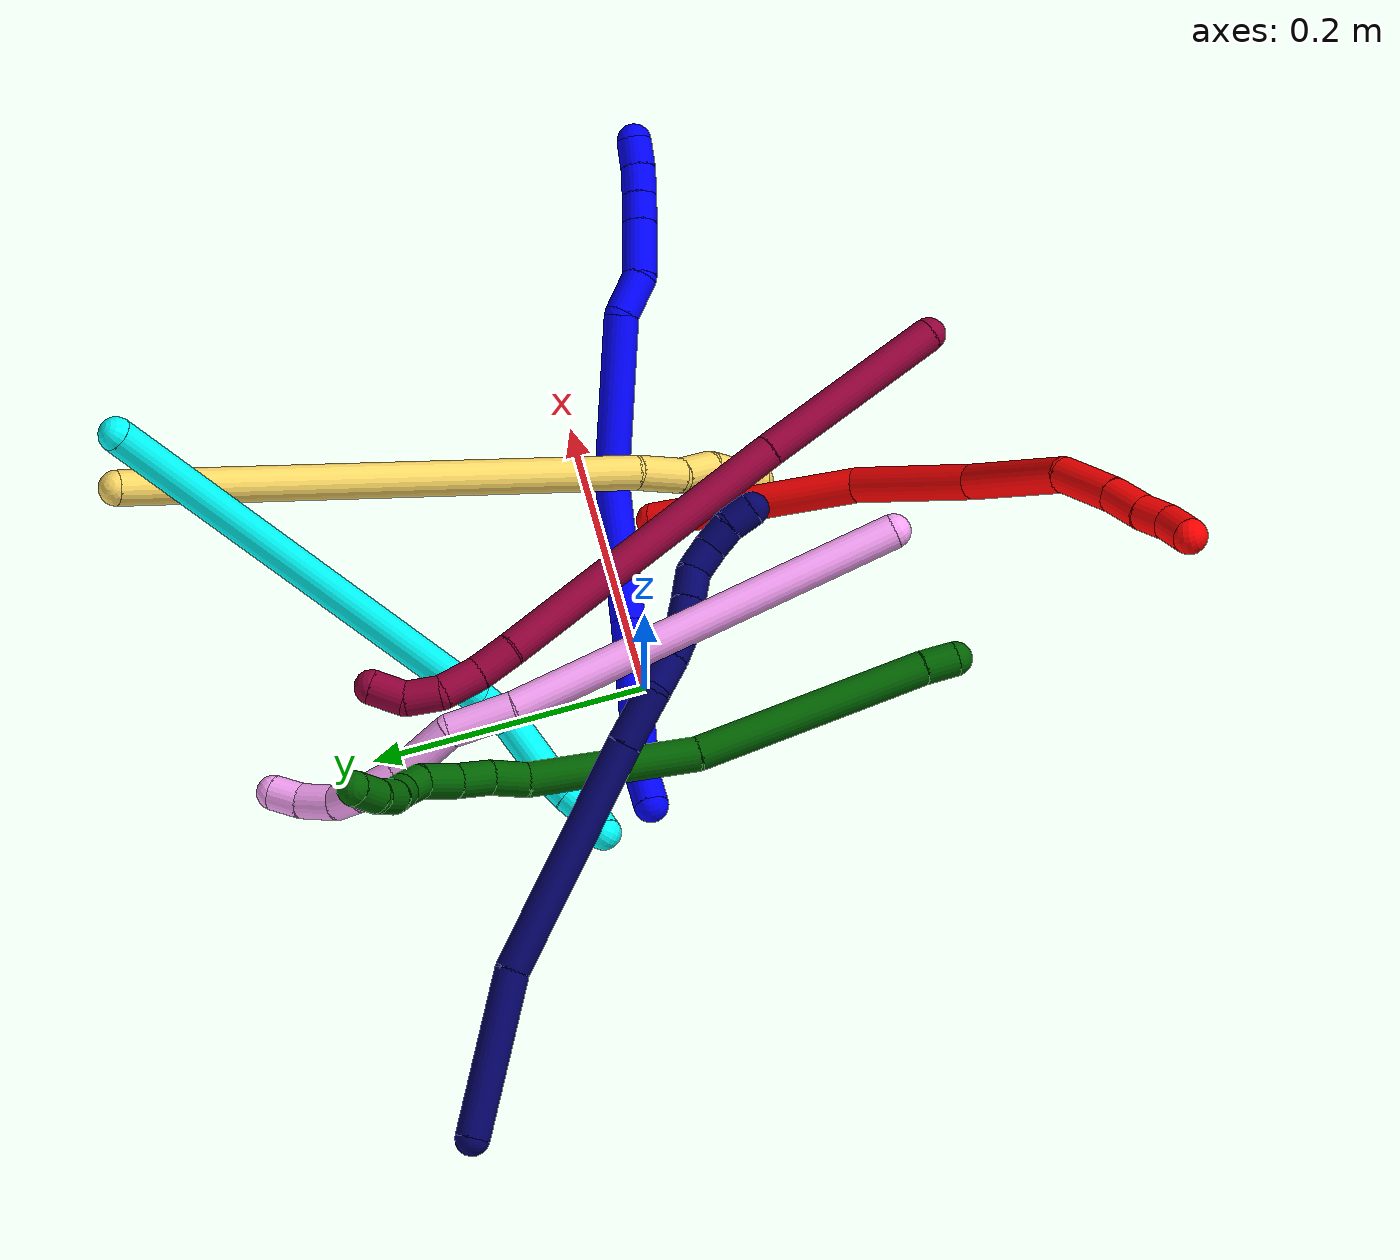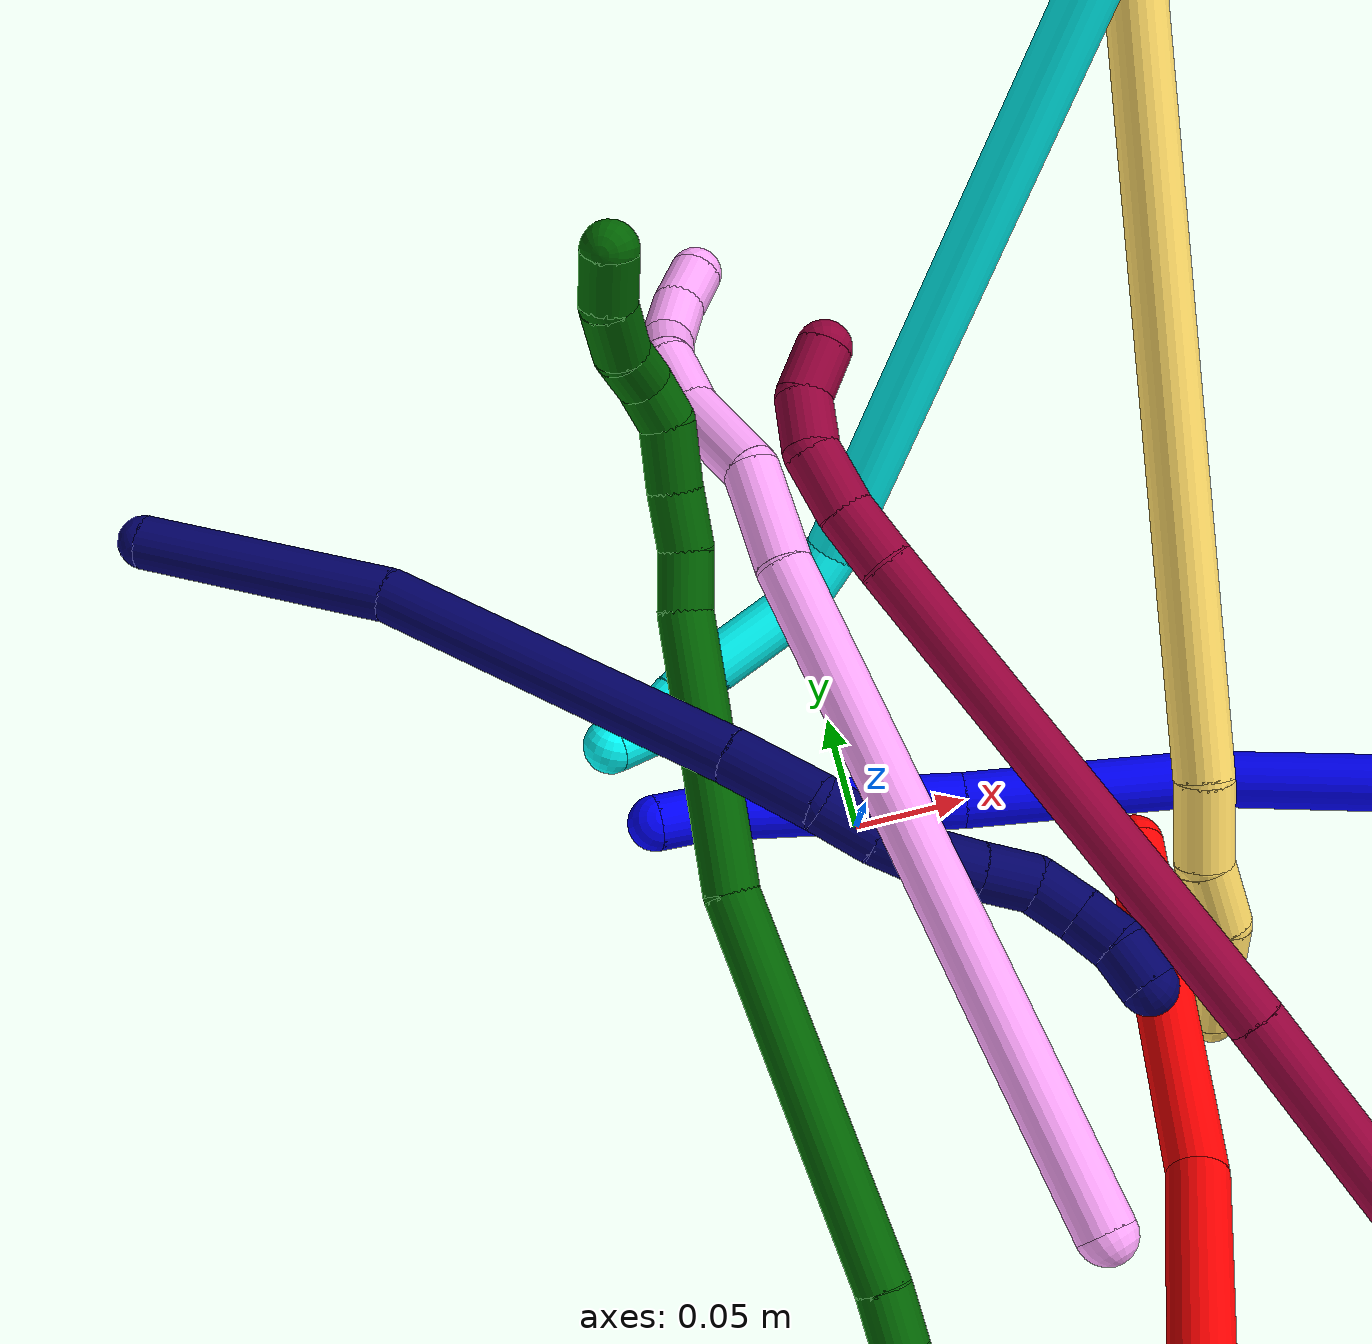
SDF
<sdf version="1.7">
 <world name="default">
  <plugin name="TubeGeneratorPlugin" filename="libtube_generator_plugin.so"/>
  <model name="photoneo_s_sensor">
   <static>1</static>
   <pose>0 0 2 1.57079 1.57079 3.14159</pose>
   <link name="link">
    <inertial><mass>0.1</mass></inertial>
    <sensor name="sensor" type="depth">
     <update_rate>30</update_rate>
     <camera>
      <horizontal_fov>1.22</horizontal_fov>
      <image><width>1920</width><height>1200</height><format>B8G8R8</format></image>
      <clip><near>0.1</near><far>4</far></clip>
      <depth_camera><output>points</output></depth_camera>
     </camera>
     <plugin name="camera_plugin" filename="libgazebo_ros_depth_camera.so">
      <baseline>0.2</baseline>
      <alwaysOn>1</alwaysOn>
      <updateRate>0.0</updateRate>
      <cameraName>camera_ir</cameraName>
      <imageTopicName>/camera/color/image_raw</imageTopicName>
      <cameraInfoTopicName>/camera/color/camera_info</cameraInfoTopicName>
      <depthImageTopicName>/camera/depth/image_raw</depthImageTopicName>
      <depthImageCameraInfoTopicName>/camera/depth/camera_info</depthImageCameraInfoTopicName>
      <pointCloudTopicName>/camera/depth/points</pointCloudTopicName>
      <frameName>fr_optical</frameName>
      <pointCloudCutoff>0.1</pointCloudCutoff>
      <pointCloudCutoffMax>2.0</pointCloudCutoffMax>
      <distortionK1>0</distortionK1>
      <distortionK2>0</distortionK2>
      <distortionK3>0</distortionK3>
      <distortionT1>0</distortionT1>
      <distortionT2>0</distortionT2>
      <CxPrime>0</CxPrime>
      <Cx>0</Cx>
      <Cy>0</Cy>
      <focalLength>0</focalLength>
      <hackBaseline>0</hackBaseline>
     </plugin>
    </sensor>
   </link>
  </model>
  <gravity>0 0 -9.8</gravity>
  <magnetic_field>6e-06 2.3e-05 -4.2e-05</magnetic_field>
  <atmosphere type="adiabatic"/>
  <physics name="default_physics" default="0" type="ode">
   <max_step_size>0.003</max_step_size>
   <real_time_factor>1</real_time_factor>
   <real_time_update_rate>1000</real_time_update_rate>
   <max_contacts>10000</max_contacts>
   <ode>
    <solver>
     <type>quick</type>
     <iters>100</iters>
     <sor>1.3</sor>
     <use_dynamic_moi_rescaling>0</use_dynamic_moi_rescaling>
    </solver>
    <constraints>
     <contact_max_correcting_vel>0</contact_max_correcting_vel>
     <contact_surface_layer>0.001</contact_surface_layer>
     <cfm>0</cfm>
     <erp>0.2</erp>
    </constraints>
   </ode>
  </physics>
  <scene><ambient>0.4 0.4 0.4 1</ambient><background>0.7 0.7 0.7 1</background><shadows>0</shadows></scene>
  <audio><device>default</device></audio>
  <spherical_coordinates>
   <surface_model>EARTH_WGS84</surface_model>
   <latitude_deg>0</latitude_deg>
   <longitude_deg>0</longitude_deg>
   <elevation>0</elevation>
   <heading_deg>0</heading_deg>
  </spherical_coordinates>
  <model name="bin">
   <static>1</static>
   <link name="bottom">
    <collision name="collision-bottom">
     <pose>0 0 -0.01 0 -0 0</pose>
     <geometry><box><size>0.8 0.6 0.02</size></box></geometry>
     <surface>
      <friction><ode><mu>100</mu><mu2>100</mu2></ode></friction>
      <contact><collide_bitmask>65535</collide_bitmask></contact>
     </surface>
    </collision>
   </link>
   <link name="west_wall">
    <collision name="collision-west_wall">
     <pose>-0.41 0 0.1 0 -0 0</pose>
     <geometry><box><size>0.02 0.6 0.2</size></box></geometry>
     <surface>
      <friction><ode><mu>100</mu><mu2>100</mu2></ode></friction>
      <contact><collide_bitmask>65535</collide_bitmask></contact>
     </surface>
    </collision>
   </link>
   <link name="east_wall">
    <collision name="collision-east_wall">
     <pose>0.41 0 0.1 0 -0 0</pose>
     <geometry><box><size>0.02 0.6 0.2</size></box></geometry>
     <surface>
      <friction><ode><mu>100</mu><mu2>100</mu2></ode></friction>
      <contact><collide_bitmask>65535</collide_bitmask></contact>
     </surface>
    </collision>
   </link>
   <link name="south_wall">
    <collision name="collision-south_wall">
     <pose>0 -0.31 0.1 0 -0 0</pose>
     <geometry><box><size>0.8 0.02 0.2</size></box></geometry>
     <surface>
      <friction><ode><mu>100</mu><mu2>100</mu2></ode></friction>
      <contact><collide_bitmask>65535</collide_bitmask></contact>
     </surface>
    </collision>
   </link>
   <link name="north_wall">
    <collision name="collision-north_wall">
     <pose>0 0.31 0.1 0 -0 0</pose>
     <geometry><box><size>0.8 0.02 0.2</size></box></geometry>
     <surface>
      <friction><ode><mu>100</mu><mu2>100</mu2></ode></friction>
      <contact><collide_bitmask>65535</collide_bitmask></contact>
     </surface>
    </collision>
   </link>
  </model>
  <model name="1">
   <static>0</static>
   <link name="1">
    <collision name="collision-cylinder-e_1_1_4">
     <pose>0.012101 -0.000627 0.001517 0.392177 1.43598 0.343613</pose>
     <geometry><cylinder><radius>0.0125</radius><length>0.024423</length></cylinder></geometry>
     <surface>
      <friction><ode><mu>1.16</mu><mu2>1.16</mu2><slip1>0</slip1><slip2>0</slip2></ode></friction>
      <contact><ode><kp>1e+06</kp><kd>1</kd><max_vel>0</max_vel><min_depth>0.001</min_depth></ode></contact>
     </surface>
    </collision>
    <visual name="visual-cylinder-e_1_1_4">
     <pose>0.012101 -0.000627 0.001517 0.392177 1.43598 0.343613</pose>
     <geometry><cylinder><radius>0.0125</radius><length>0.024423</length></cylinder></geometry>
     <material><ambient>0 0 1 1</ambient></material>
    </visual>
    <collision name="collision-cylinder-e_2_4_5">
     <pose>0.077294 -0.01362 0.019102 0.655877 1.206 0.460221</pose>
     <geometry><cylinder><radius>0.0125</radius><length>0.113665</length></cylinder></geometry>
     <surface>
      <friction><ode><mu>1.16</mu><mu2>1.16</mu2><slip1>0</slip1><slip2>0</slip2></ode></friction>
      <contact><ode><kp>1e+06</kp><kd>1</kd><max_vel>0</max_vel><min_depth>0.001</min_depth></ode></contact>
     </surface>
    </collision>
    <visual name="visual-cylinder-e_2_4_5">
     <pose>0.077294 -0.01362 0.019102 0.655877 1.206 0.460221</pose>
     <geometry><cylinder><radius>0.0125</radius><length>0.113665</length></cylinder></geometry>
     <material><ambient>0 0 1 1</ambient></material>
    </visual>
    <collision name="collision-cylinder-e_3_5_6">
     <pose>0.178478 -0.035902 0.05471 0.469662 1.14326 0.305404</pose>
     <geometry><cylinder><radius>0.0125</radius><length>0.105696</length></cylinder></geometry>
     <surface>
      <friction><ode><mu>1.16</mu><mu2>1.16</mu2><slip1>0</slip1><slip2>0</slip2></ode></friction>
      <contact><ode><kp>1e+06</kp><kd>1</kd><max_vel>0</max_vel><min_depth>0.001</min_depth></ode></contact>
     </surface>
    </collision>
    <visual name="visual-cylinder-e_3_5_6">
     <pose>0.178478 -0.035902 0.05471 0.469662 1.14326 0.305404</pose>
     <geometry><cylinder><radius>0.0125</radius><length>0.105696</length></cylinder></geometry>
     <material><ambient>0 0 1 1</ambient></material>
    </visual>
    <collision name="collision-cylinder-e_4_6_7">
     <pose>0.271136 -0.065005 0.107903 0.518151 0.855248 0.240411</pose>
     <geometry><cylinder><radius>0.0125</radius><length>0.118099</length></cylinder></geometry>
     <surface>
      <friction><ode><mu>1.16</mu><mu2>1.16</mu2><slip1>0</slip1><slip2>0</slip2></ode></friction>
      <contact><ode><kp>1e+06</kp><kd>1</kd><max_vel>0</max_vel><min_depth>0.001</min_depth></ode></contact>
     </surface>
    </collision>
    <visual name="visual-cylinder-e_4_6_7">
     <pose>0.271136 -0.065005 0.107903 0.518151 0.855248 0.240411</pose>
     <geometry><cylinder><radius>0.0125</radius><length>0.118099</length></cylinder></geometry>
     <material><ambient>0 0 1 1</ambient></material>
    </visual>
    <collision name="collision-cylinder-e_5_7_8">
     <pose>0.327197 -0.094861 0.145277 1.23525 0.793931 0.578849</pose>
     <geometry><cylinder><radius>0.0125</radius><length>0.032238</length></cylinder></geometry>
     <surface>
      <friction><ode><mu>1.16</mu><mu2>1.16</mu2><slip1>0</slip1><slip2>0</slip2></ode></friction>
      <contact><ode><kp>1e+06</kp><kd>1</kd><max_vel>0</max_vel><min_depth>0.001</min_depth></ode></contact>
     </surface>
    </collision>
    <visual name="visual-cylinder-e_5_7_8">
     <pose>0.327197 -0.094861 0.145277 1.23525 0.793931 0.578849</pose>
     <geometry><cylinder><radius>0.0125</radius><length>0.032238</length></cylinder></geometry>
     <material><ambient>0 0 1 1</ambient></material>
    </visual>
    <collision name="collision-cylinder-e_6_8_9">
     <pose>0.35812 -0.111949 0.153613 0.947343 1.1844 0.664151</pose>
     <geometry><cylinder><radius>0.0125</radius><length>0.041948</length></cylinder></geometry>
     <surface>
      <friction><ode><mu>1.16</mu><mu2>1.16</mu2><slip1>0</slip1><slip2>0</slip2></ode></friction>
      <contact><ode><kp>1e+06</kp><kd>1</kd><max_vel>0</max_vel><min_depth>0.001</min_depth></ode></contact>
     </surface>
    </collision>
    <visual name="visual-cylinder-e_6_8_9">
     <pose>0.35812 -0.111949 0.153613 0.947343 1.1844 0.664151</pose>
     <geometry><cylinder><radius>0.0125</radius><length>0.041948</length></cylinder></geometry>
     <material><ambient>0 0 1 1</ambient></material>
    </visual>
    <collision name="collision-cylinder-e_7_9_10">
     <pose>0.387473 -0.121516 0.161301 0.797885 1.15347 0.535286</pose>
     <geometry><cylinder><radius>0.0125</radius><length>0.021715</length></cylinder></geometry>
     <surface>
      <friction><ode><mu>1.16</mu><mu2>1.16</mu2><slip1>0</slip1><slip2>0</slip2></ode></friction>
      <contact><ode><kp>1e+06</kp><kd>1</kd><max_vel>0</max_vel><min_depth>0.001</min_depth></ode></contact>
     </surface>
    </collision>
    <visual name="visual-cylinder-e_7_9_10">
     <pose>0.387473 -0.121516 0.161301 0.797885 1.15347 0.535286</pose>
     <geometry><cylinder><radius>0.0125</radius><length>0.021715</length></cylinder></geometry>
     <material><ambient>0 0 1 1</ambient></material>
    </visual>
    <collision name="collision-cylinder-e_8_10_11">
     <pose>0.407068 -0.127409 0.167824 0.67157 1.14308 0.441599</pose>
     <geometry><cylinder><radius>0.0125</radius><length>0.021252</length></cylinder></geometry>
     <surface>
      <friction><ode><mu>1.16</mu><mu2>1.16</mu2><slip1>0</slip1><slip2>0</slip2></ode></friction>
      <contact><ode><kp>1e+06</kp><kd>1</kd><max_vel>0</max_vel><min_depth>0.001</min_depth></ode></contact>
     </surface>
    </collision>
    <visual name="visual-cylinder-e_8_10_11">
     <pose>0.407068 -0.127409 0.167824 0.67157 1.14308 0.441599</pose>
     <geometry><cylinder><radius>0.0125</radius><length>0.021252</length></cylinder></geometry>
     <material><ambient>0 0 1 1</ambient></material>
    </visual>
    <collision name="collision-cylinder-e_9_11_2">
     <pose>0.426346 -0.131838 0.175106 0.414609 1.15989 0.273841</pose>
     <geometry><cylinder><radius>0.0125</radius><length>0.020964</length></cylinder></geometry>
     <surface>
      <friction><ode><mu>1.16</mu><mu2>1.16</mu2><slip1>0</slip1><slip2>0</slip2></ode></friction>
      <contact><ode><kp>1e+06</kp><kd>1</kd><max_vel>0</max_vel><min_depth>0.001</min_depth></ode></contact>
     </surface>
    </collision>
    <visual name="visual-cylinder-e_9_11_2">
     <pose>0.426346 -0.131838 0.175106 0.414609 1.15989 0.273841</pose>
     <geometry><cylinder><radius>0.0125</radius><length>0.020964</length></cylinder></geometry>
     <material><ambient>0 0 1 1</ambient></material>
    </visual>
    <collision name="collision-sphere-2">
     <pose>0.435955 -0.133525 0.178938 0 -0 0</pose>
     <geometry><sphere><radius>0.0125</radius></sphere></geometry>
     <surface>
      <friction><ode><mu>1.16</mu><mu2>1.16</mu2><slip1>0</slip1><slip2>0</slip2></ode></friction>
      <contact><ode><kp>1e+06</kp><kd>1</kd><max_vel>0</max_vel><min_depth>0.001</min_depth></ode></contact>
     </surface>
    </collision>
    <visual name="visual-sphere-2">
     <pose>0.435955 -0.133525 0.178938 0 -0 0</pose>
     <geometry><sphere><radius>0.0125</radius></sphere></geometry>
     <material><ambient>0 0 1 1</ambient></material>
    </visual>
    <collision name="collision-sphere-11">
     <pose>0.416736 -0.130151 0.171274 0 -0 0</pose>
     <geometry><sphere><radius>0.0125</radius></sphere></geometry>
     <surface>
      <friction><ode><mu>1.16</mu><mu2>1.16</mu2><slip1>0</slip1><slip2>0</slip2></ode></friction>
      <contact><ode><kp>1e+06</kp><kd>1</kd><max_vel>0</max_vel><min_depth>0.001</min_depth></ode></contact>
     </surface>
    </collision>
    <visual name="visual-sphere-11">
     <pose>0.416736 -0.130151 0.171274 0 -0 0</pose>
     <geometry><sphere><radius>0.0125</radius></sphere></geometry>
     <material><ambient>0 0 1 1</ambient></material>
    </visual>
    <collision name="collision-sphere-10">
     <pose>0.397399 -0.124666 0.164373 0 -0 0</pose>
     <geometry><sphere><radius>0.0125</radius></sphere></geometry>
     <surface>
      <friction><ode><mu>1.16</mu><mu2>1.16</mu2><slip1>0</slip1><slip2>0</slip2></ode></friction>
      <contact><ode><kp>1e+06</kp><kd>1</kd><max_vel>0</max_vel><min_depth>0.001</min_depth></ode></contact>
     </surface>
    </collision>
    <visual name="visual-sphere-10">
     <pose>0.397399 -0.124666 0.164373 0 -0 0</pose>
     <geometry><sphere><radius>0.0125</radius></sphere></geometry>
     <material><ambient>0 0 1 1</ambient></material>
    </visual>
    <collision name="collision-sphere-9">
     <pose>0.377547 -0.118366 0.158228 0 -0 0</pose>
     <geometry><sphere><radius>0.0125</radius></sphere></geometry>
     <surface>
      <friction><ode><mu>1.16</mu><mu2>1.16</mu2><slip1>0</slip1><slip2>0</slip2></ode></friction>
      <contact><ode><kp>1e+06</kp><kd>1</kd><max_vel>0</max_vel><min_depth>0.001</min_depth></ode></contact>
     </surface>
    </collision>
    <visual name="visual-sphere-9">
     <pose>0.377547 -0.118366 0.158228 0 -0 0</pose>
     <geometry><sphere><radius>0.0125</radius></sphere></geometry>
     <material><ambient>0 0 1 1</ambient></material>
    </visual>
    <collision name="collision-sphere-4">
     <pose>0.024202 -0.001255 0.003033 0 -0 0</pose>
     <geometry><sphere><radius>0.0125</radius></sphere></geometry>
     <surface>
      <friction><ode><mu>1.16</mu><mu2>1.16</mu2><slip1>0</slip1><slip2>0</slip2></ode></friction>
      <contact><ode><kp>1e+06</kp><kd>1</kd><max_vel>0</max_vel><min_depth>0.001</min_depth></ode></contact>
     </surface>
    </collision>
    <visual name="visual-sphere-4">
     <pose>0.024202 -0.001255 0.003033 0 -0 0</pose>
     <geometry><sphere><radius>0.0125</radius></sphere></geometry>
     <material><ambient>0 0 1 1</ambient></material>
    </visual>
    <collision name="collision-sphere-1">
     <geometry><sphere><radius>0.0125</radius></sphere></geometry>
     <surface>
      <friction><ode><mu>1.16</mu><mu2>1.16</mu2><slip1>0</slip1><slip2>0</slip2></ode></friction>
      <contact><ode><kp>1e+06</kp><kd>1</kd><max_vel>0</max_vel><min_depth>0.001</min_depth></ode></contact>
     </surface>
    </collision>
    <visual name="visual-sphere-1">
     <geometry><sphere><radius>0.0125</radius></sphere></geometry>
     <material><ambient>0 0 1 1</ambient></material>
    </visual>
    <collision name="collision-sphere-8">
     <pose>0.338692 -0.105531 0.148998 0 -0 0</pose>
     <geometry><sphere><radius>0.0125</radius></sphere></geometry>
     <surface>
      <friction><ode><mu>1.16</mu><mu2>1.16</mu2><slip1>0</slip1><slip2>0</slip2></ode></friction>
      <contact><ode><kp>1e+06</kp><kd>1</kd><max_vel>0</max_vel><min_depth>0.001</min_depth></ode></contact>
     </surface>
    </collision>
    <visual name="visual-sphere-8">
     <pose>0.338692 -0.105531 0.148998 0 -0 0</pose>
     <geometry><sphere><radius>0.0125</radius></sphere></geometry>
     <material><ambient>0 0 1 1</ambient></material>
    </visual>
    <collision name="collision-sphere-5">
     <pose>0.130387 -0.025985 0.035171 0 -0 0</pose>
     <geometry><sphere><radius>0.0125</radius></sphere></geometry>
     <surface>
      <friction><ode><mu>1.16</mu><mu2>1.16</mu2><slip1>0</slip1><slip2>0</slip2></ode></friction>
      <contact><ode><kp>1e+06</kp><kd>1</kd><max_vel>0</max_vel><min_depth>0.001</min_depth></ode></contact>
     </surface>
    </collision>
    <visual name="visual-sphere-5">
     <pose>0.130387 -0.025985 0.035171 0 -0 0</pose>
     <geometry><sphere><radius>0.0125</radius></sphere></geometry>
     <material><ambient>0 0 1 1</ambient></material>
    </visual>
    <collision name="collision-sphere-6">
     <pose>0.226569 -0.045819 0.07425 0 -0 0</pose>
     <geometry><sphere><radius>0.0125</radius></sphere></geometry>
     <surface>
      <friction><ode><mu>1.16</mu><mu2>1.16</mu2><slip1>0</slip1><slip2>0</slip2></ode></friction>
      <contact><ode><kp>1e+06</kp><kd>1</kd><max_vel>0</max_vel><min_depth>0.001</min_depth></ode></contact>
     </surface>
    </collision>
    <visual name="visual-sphere-6">
     <pose>0.226569 -0.045819 0.07425 0 -0 0</pose>
     <geometry><sphere><radius>0.0125</radius></sphere></geometry>
     <material><ambient>0 0 1 1</ambient></material>
    </visual>
    <collision name="collision-sphere-7">
     <pose>0.315703 -0.084191 0.141556 0 -0 0</pose>
     <geometry><sphere><radius>0.0125</radius></sphere></geometry>
     <surface>
      <friction><ode><mu>1.16</mu><mu2>1.16</mu2><slip1>0</slip1><slip2>0</slip2></ode></friction>
      <contact><ode><kp>1e+06</kp><kd>1</kd><max_vel>0</max_vel><min_depth>0.001</min_depth></ode></contact>
     </surface>
    </collision>
    <visual name="visual-sphere-7">
     <pose>0.315703 -0.084191 0.141556 0 -0 0</pose>
     <geometry><sphere><radius>0.0125</radius></sphere></geometry>
     <material><ambient>0 0 1 1</ambient></material>
    </visual>
    <inertial>
     <pose>0.22308 -0.057799 0.085203 0 -0 0</pose>
     <mass>0.5</mass>
     <inertia>
      <ixx>0.000272</ixx>
      <ixy>0</ixy>
      <ixz>0</ixz>
      <iyy>0.00042</iyy>
      <iyz>0</iyz>
      <izz>-0.000222</izz>
     </inertia>
    </inertial>
   </link>
   <pose>-0.087318 0.019626 0.016431 0.069956 0.325902 0.056881</pose>
  </model>
  <model name="2">
   <static>0</static>
   <link name="2">
    <collision name="collision-cylinder-e_1_1_4">
     <pose>0.000123 0.001715 0.078644 -0.021802 0.001563 -1.7e-05</pose>
     <geometry><cylinder><radius>0.0125</radius><length>0.157325</length></cylinder></geometry>
     <surface>
      <friction><ode><mu>1.16</mu><mu2>1.16</mu2><slip1>0</slip1><slip2>0</slip2></ode></friction>
      <contact><ode><kp>1e+06</kp><kd>1</kd><max_vel>0</max_vel><min_depth>0.001</min_depth></ode></contact>
     </surface>
    </collision>
    <visual name="visual-cylinder-e_1_1_4">
     <pose>0.000123 0.001715 0.078644 -0.021802 0.001563 -1.7e-05</pose>
     <geometry><cylinder><radius>0.0125</radius><length>0.157325</length></cylinder></geometry>
     <material><ambient>1 0 0 1</ambient></material>
    </visual>
    <collision name="collision-cylinder-e_2_4_5">
     <pose>-0.004645 -0.011169 0.205609 0.293395 -0.096586 -0.014282</pose>
     <geometry><cylinder><radius>0.0125</radius><length>0.10143</length></cylinder></geometry>
     <surface>
      <friction><ode><mu>1.16</mu><mu2>1.16</mu2><slip1>0</slip1><slip2>0</slip2></ode></friction>
      <contact><ode><kp>1e+06</kp><kd>1</kd><max_vel>0</max_vel><min_depth>0.001</min_depth></ode></contact>
     </surface>
    </collision>
    <visual name="visual-cylinder-e_2_4_5">
     <pose>-0.004645 -0.011169 0.205609 0.293395 -0.096586 -0.014282</pose>
     <geometry><cylinder><radius>0.0125</radius><length>0.10143</length></cylinder></geometry>
     <material><ambient>1 0 0 1</ambient></material>
    </visual>
    <collision name="collision-cylinder-e_3_5_6">
     <pose>-0.026371 -0.051005 0.297753 0.522515 -0.321368 -0.086617</pose>
     <geometry><cylinder><radius>0.0125</radius><length>0.106598</length></cylinder></geometry>
     <surface>
      <friction><ode><mu>1.16</mu><mu2>1.16</mu2><slip1>0</slip1><slip2>0</slip2></ode></friction>
      <contact><ode><kp>1e+06</kp><kd>1</kd><max_vel>0</max_vel><min_depth>0.001</min_depth></ode></contact>
     </surface>
    </collision>
    <visual name="visual-cylinder-e_3_5_6">
     <pose>-0.026371 -0.051005 0.297753 0.522515 -0.321368 -0.086617</pose>
     <geometry><cylinder><radius>0.0125</radius><length>0.106598</length></cylinder></geometry>
     <material><ambient>1 0 0 1</ambient></material>
    </visual>
    <collision name="collision-cylinder-e_4_6_7">
     <pose>-0.043287 -0.091571 0.36221 0.638892 -0.003131 -0.001036</pose>
     <geometry><cylinder><radius>0.0125</radius><length>0.051409</length></cylinder></geometry>
     <surface>
      <friction><ode><mu>1.16</mu><mu2>1.16</mu2><slip1>0</slip1><slip2>0</slip2></ode></friction>
      <contact><ode><kp>1e+06</kp><kd>1</kd><max_vel>0</max_vel><min_depth>0.001</min_depth></ode></contact>
     </surface>
    </collision>
    <visual name="visual-cylinder-e_4_6_7">
     <pose>-0.043287 -0.091571 0.36221 0.638892 -0.003131 -0.001036</pose>
     <geometry><cylinder><radius>0.0125</radius><length>0.051409</length></cylinder></geometry>
     <material><ambient>1 0 0 1</ambient></material>
    </visual>
    <collision name="collision-cylinder-e_5_7_8">
     <pose>-0.042567 -0.117716 0.394918 0.730582 0.049312 0.018863</pose>
     <geometry><cylinder><radius>0.0125</radius><length>0.032462</length></cylinder></geometry>
     <surface>
      <friction><ode><mu>1.16</mu><mu2>1.16</mu2><slip1>0</slip1><slip2>0</slip2></ode></friction>
      <contact><ode><kp>1e+06</kp><kd>1</kd><max_vel>0</max_vel><min_depth>0.001</min_depth></ode></contact>
     </surface>
    </collision>
    <visual name="visual-cylinder-e_5_7_8">
     <pose>-0.042567 -0.117716 0.394918 0.730582 0.049312 0.018863</pose>
     <geometry><cylinder><radius>0.0125</radius><length>0.032462</length></cylinder></geometry>
     <material><ambient>1 0 0 1</ambient></material>
    </visual>
    <collision name="collision-cylinder-e_6_8_9">
     <pose>-0.04125 -0.135214 0.416818 0.597041 0.043469 0.013378</pose>
     <geometry><cylinder><radius>0.0125</radius><length>0.023786</length></cylinder></geometry>
     <surface>
      <friction><ode><mu>1.16</mu><mu2>1.16</mu2><slip1>0</slip1><slip2>0</slip2></ode></friction>
      <contact><ode><kp>1e+06</kp><kd>1</kd><max_vel>0</max_vel><min_depth>0.001</min_depth></ode></contact>
     </surface>
    </collision>
    <visual name="visual-cylinder-e_6_8_9">
     <pose>-0.04125 -0.135214 0.416818 0.597041 0.043469 0.013378</pose>
     <geometry><cylinder><radius>0.0125</radius><length>0.023786</length></cylinder></geometry>
     <material><ambient>1 0 0 1</ambient></material>
    </visual>
    <collision name="collision-cylinder-e_7_9_2">
     <pose>-0.041769 -0.15179 0.435761 0.826381 -0.076819 -0.033693</pose>
     <geometry><cylinder><radius>0.0125</radius><length>0.02699</length></cylinder></geometry>
     <surface>
      <friction><ode><mu>1.16</mu><mu2>1.16</mu2><slip1>0</slip1><slip2>0</slip2></ode></friction>
      <contact><ode><kp>1e+06</kp><kd>1</kd><max_vel>0</max_vel><min_depth>0.001</min_depth></ode></contact>
     </surface>
    </collision>
    <visual name="visual-cylinder-e_7_9_2">
     <pose>-0.041769 -0.15179 0.435761 0.826381 -0.076819 -0.033693</pose>
     <geometry><cylinder><radius>0.0125</radius><length>0.02699</length></cylinder></geometry>
     <material><ambient>1 0 0 1</ambient></material>
    </visual>
    <collision name="collision-sphere-2">
     <pose>-0.042805 -0.161686 0.444878 0 -0 0</pose>
     <geometry><sphere><radius>0.0125</radius></sphere></geometry>
     <surface>
      <friction><ode><mu>1.16</mu><mu2>1.16</mu2><slip1>0</slip1><slip2>0</slip2></ode></friction>
      <contact><ode><kp>1e+06</kp><kd>1</kd><max_vel>0</max_vel><min_depth>0.001</min_depth></ode></contact>
     </surface>
    </collision>
    <visual name="visual-sphere-2">
     <pose>-0.042805 -0.161686 0.444878 0 -0 0</pose>
     <geometry><sphere><radius>0.0125</radius></sphere></geometry>
     <material><ambient>1 0 0 1</ambient></material>
    </visual>
    <collision name="collision-sphere-9">
     <pose>-0.040733 -0.141894 0.426645 0 -0 0</pose>
     <geometry><sphere><radius>0.0125</radius></sphere></geometry>
     <surface>
      <friction><ode><mu>1.16</mu><mu2>1.16</mu2><slip1>0</slip1><slip2>0</slip2></ode></friction>
      <contact><ode><kp>1e+06</kp><kd>1</kd><max_vel>0</max_vel><min_depth>0.001</min_depth></ode></contact>
     </surface>
    </collision>
    <visual name="visual-sphere-9">
     <pose>-0.040733 -0.141894 0.426645 0 -0 0</pose>
     <geometry><sphere><radius>0.0125</radius></sphere></geometry>
     <material><ambient>1 0 0 1</ambient></material>
    </visual>
    <collision name="collision-sphere-4">
     <pose>0.000246 0.00343 0.157287 0 -0 0</pose>
     <geometry><sphere><radius>0.0125</radius></sphere></geometry>
     <surface>
      <friction><ode><mu>1.16</mu><mu2>1.16</mu2><slip1>0</slip1><slip2>0</slip2></ode></friction>
      <contact><ode><kp>1e+06</kp><kd>1</kd><max_vel>0</max_vel><min_depth>0.001</min_depth></ode></contact>
     </surface>
    </collision>
    <visual name="visual-sphere-4">
     <pose>0.000246 0.00343 0.157287 0 -0 0</pose>
     <geometry><sphere><radius>0.0125</radius></sphere></geometry>
     <material><ambient>1 0 0 1</ambient></material>
    </visual>
    <collision name="collision-sphere-1">
     <geometry><sphere><radius>0.0125</radius></sphere></geometry>
     <surface>
      <friction><ode><mu>1.16</mu><mu2>1.16</mu2><slip1>0</slip1><slip2>0</slip2></ode></friction>
      <contact><ode><kp>1e+06</kp><kd>1</kd><max_vel>0</max_vel><min_depth>0.001</min_depth></ode></contact>
     </surface>
    </collision>
    <visual name="visual-sphere-1">
     <geometry><sphere><radius>0.0125</radius></sphere></geometry>
     <material><ambient>1 0 0 1</ambient></material>
    </visual>
    <collision name="collision-sphere-8">
     <pose>-0.041767 -0.128534 0.406992 0 -0 0</pose>
     <geometry><sphere><radius>0.0125</radius></sphere></geometry>
     <surface>
      <friction><ode><mu>1.16</mu><mu2>1.16</mu2><slip1>0</slip1><slip2>0</slip2></ode></friction>
      <contact><ode><kp>1e+06</kp><kd>1</kd><max_vel>0</max_vel><min_depth>0.001</min_depth></ode></contact>
     </surface>
    </collision>
    <visual name="visual-sphere-8">
     <pose>-0.041767 -0.128534 0.406992 0 -0 0</pose>
     <geometry><sphere><radius>0.0125</radius></sphere></geometry>
     <material><ambient>1 0 0 1</ambient></material>
    </visual>
    <collision name="collision-sphere-5">
     <pose>-0.009536 -0.025768 0.253931 0 -0 0</pose>
     <geometry><sphere><radius>0.0125</radius></sphere></geometry>
     <surface>
      <friction><ode><mu>1.16</mu><mu2>1.16</mu2><slip1>0</slip1><slip2>0</slip2></ode></friction>
      <contact><ode><kp>1e+06</kp><kd>1</kd><max_vel>0</max_vel><min_depth>0.001</min_depth></ode></contact>
     </surface>
    </collision>
    <visual name="visual-sphere-5">
     <pose>-0.009536 -0.025768 0.253931 0 -0 0</pose>
     <geometry><sphere><radius>0.0125</radius></sphere></geometry>
     <material><ambient>1 0 0 1</ambient></material>
    </visual>
    <collision name="collision-sphere-6">
     <pose>-0.043206 -0.076243 0.341576 0 -0 0</pose>
     <geometry><sphere><radius>0.0125</radius></sphere></geometry>
     <surface>
      <friction><ode><mu>1.16</mu><mu2>1.16</mu2><slip1>0</slip1><slip2>0</slip2></ode></friction>
      <contact><ode><kp>1e+06</kp><kd>1</kd><max_vel>0</max_vel><min_depth>0.001</min_depth></ode></contact>
     </surface>
    </collision>
    <visual name="visual-sphere-6">
     <pose>-0.043206 -0.076243 0.341576 0 -0 0</pose>
     <geometry><sphere><radius>0.0125</radius></sphere></geometry>
     <material><ambient>1 0 0 1</ambient></material>
    </visual>
    <collision name="collision-sphere-7">
     <pose>-0.043367 -0.106898 0.382844 0 -0 0</pose>
     <geometry><sphere><radius>0.0125</radius></sphere></geometry>
     <surface>
      <friction><ode><mu>1.16</mu><mu2>1.16</mu2><slip1>0</slip1><slip2>0</slip2></ode></friction>
      <contact><ode><kp>1e+06</kp><kd>1</kd><max_vel>0</max_vel><min_depth>0.001</min_depth></ode></contact>
     </surface>
    </collision>
    <visual name="visual-sphere-7">
     <pose>-0.043367 -0.106898 0.382844 0 -0 0</pose>
     <geometry><sphere><radius>0.0125</radius></sphere></geometry>
     <material><ambient>1 0 0 1</ambient></material>
    </visual>
    <inertial>
     <pose>-0.017957 -0.044284 0.236168 0 -0 0</pose>
     <mass>0.5</mass>
     <inertia>
      <ixx>0.000529</ixx>
      <ixy>0</ixy>
      <ixz>0</ixz>
      <iyy>0.000505</iyy>
      <iyz>0</iyz>
      <izz>0.000159</izz>
     </inertia>
    </inertial>
   </link>
   <pose>0.115533 -0.038536 0.011485 -0.89335 0.852437 -2.83342</pose>
  </model>
  <model name="3">
   <static>0</static>
   <link name="3">
    <collision name="collision-cylinder-e_1_1_4">
     <pose>-0.019446 0.00034 -0.180207 -3.13971 -0.10749 3.10655</pose>
     <geometry><cylinder><radius>0.0125</radius><length>0.362508</length></cylinder></geometry>
     <surface>
      <friction><ode><mu>1.16</mu><mu2>1.16</mu2><slip1>0</slip1><slip2>0</slip2></ode></friction>
      <contact><ode><kp>1e+06</kp><kd>1</kd><max_vel>0</max_vel><min_depth>0.001</min_depth></ode></contact>
     </surface>
    </collision>
    <visual name="visual-cylinder-e_1_1_4">
     <pose>-0.019446 0.00034 -0.180207 -3.13971 -0.10749 3.10655</pose>
     <geometry><cylinder><radius>0.0125</radius><length>0.362508</length></cylinder></geometry>
     <material><ambient>0.003922 1 0.996078 1</ambient></material>
    </visual>
    <collision name="collision-cylinder-e_2_4_5">
     <pose>-0.04101 -0.004914 -0.37501 2.7756 -0.134769 -0.699348</pose>
     <geometry><cylinder><radius>0.0125</radius><length>0.031547</length></cylinder></geometry>
     <surface>
      <friction><ode><mu>1.16</mu><mu2>1.16</mu2><slip1>0</slip1><slip2>0</slip2></ode></friction>
      <contact><ode><kp>1e+06</kp><kd>1</kd><max_vel>0</max_vel><min_depth>0.001</min_depth></ode></contact>
     </surface>
    </collision>
    <visual name="visual-cylinder-e_2_4_5">
     <pose>-0.04101 -0.004914 -0.37501 2.7756 -0.134769 -0.699348</pose>
     <geometry><cylinder><radius>0.0125</radius><length>0.031547</length></cylinder></geometry>
     <material><ambient>0.003922 1 0.996078 1</ambient></material>
    </visual>
    <collision name="collision-cylinder-e_3_5_6">
     <pose>-0.051284 -0.024239 -0.405723 2.43598 -0.367616 -0.935101</pose>
     <geometry><cylinder><radius>0.0125</radius><length>0.045377</length></cylinder></geometry>
     <surface>
      <friction><ode><mu>1.16</mu><mu2>1.16</mu2><slip1>0</slip1><slip2>0</slip2></ode></friction>
      <contact><ode><kp>1e+06</kp><kd>1</kd><max_vel>0</max_vel><min_depth>0.001</min_depth></ode></contact>
     </surface>
    </collision>
    <visual name="visual-cylinder-e_3_5_6">
     <pose>-0.051284 -0.024239 -0.405723 2.43598 -0.367616 -0.935101</pose>
     <geometry><cylinder><radius>0.0125</radius><length>0.045377</length></cylinder></geometry>
     <material><ambient>0.003922 1 0.996078 1</ambient></material>
    </visual>
    <collision name="collision-cylinder-e_4_6_7">
     <pose>-0.061644 -0.044902 -0.428959 2.36947 -0.218491 -0.52714</pose>
     <geometry><cylinder><radius>0.0125</radius><length>0.020358</length></cylinder></geometry>
     <surface>
      <friction><ode><mu>1.16</mu><mu2>1.16</mu2><slip1>0</slip1><slip2>0</slip2></ode></friction>
      <contact><ode><kp>1e+06</kp><kd>1</kd><max_vel>0</max_vel><min_depth>0.001</min_depth></ode></contact>
     </surface>
    </collision>
    <visual name="visual-cylinder-e_4_6_7">
     <pose>-0.061644 -0.044902 -0.428959 2.36947 -0.218491 -0.52714</pose>
     <geometry><cylinder><radius>0.0125</radius><length>0.020358</length></cylinder></geometry>
     <material><ambient>0.003922 1 0.996078 1</ambient></material>
    </visual>
    <collision name="collision-cylinder-e_5_7_8">
     <pose>-0.065011 -0.058985 -0.443066 2.34475 -0.115571 -0.273156</pose>
     <geometry><cylinder><radius>0.0125</radius><length>0.02013</length></cylinder></geometry>
     <surface>
      <friction><ode><mu>1.16</mu><mu2>1.16</mu2><slip1>0</slip1><slip2>0</slip2></ode></friction>
      <contact><ode><kp>1e+06</kp><kd>1</kd><max_vel>0</max_vel><min_depth>0.001</min_depth></ode></contact>
     </surface>
    </collision>
    <visual name="visual-cylinder-e_5_7_8">
     <pose>-0.065011 -0.058985 -0.443066 2.34475 -0.115571 -0.273156</pose>
     <geometry><cylinder><radius>0.0125</radius><length>0.02013</length></cylinder></geometry>
     <material><ambient>0.003922 1 0.996078 1</ambient></material>
    </visual>
    <collision name="collision-cylinder-e_6_8_2">
     <pose>-0.068842 -0.07536 -0.45298 1.87788 -0.269162 -0.365827</pose>
     <geometry><cylinder><radius>0.0125</radius><length>0.02008</length></cylinder></geometry>
     <surface>
      <friction><ode><mu>1.16</mu><mu2>1.16</mu2><slip1>0</slip1><slip2>0</slip2></ode></friction>
      <contact><ode><kp>1e+06</kp><kd>1</kd><max_vel>0</max_vel><min_depth>0.001</min_depth></ode></contact>
     </surface>
    </collision>
    <visual name="visual-cylinder-e_6_8_2">
     <pose>-0.068842 -0.07536 -0.45298 1.87788 -0.269162 -0.365827</pose>
     <geometry><cylinder><radius>0.0125</radius><length>0.02008</length></cylinder></geometry>
     <material><ambient>0.003922 1 0.996078 1</ambient></material>
    </visual>
    <collision name="collision-sphere-2">
     <pose>-0.071512 -0.084586 -0.455905 0 -0 0</pose>
     <geometry><sphere><radius>0.0125</radius></sphere></geometry>
     <surface>
      <friction><ode><mu>1.16</mu><mu2>1.16</mu2><slip1>0</slip1><slip2>0</slip2></ode></friction>
      <contact><ode><kp>1e+06</kp><kd>1</kd><max_vel>0</max_vel><min_depth>0.001</min_depth></ode></contact>
     </surface>
    </collision>
    <visual name="visual-sphere-2">
     <pose>-0.071512 -0.084586 -0.455905 0 -0 0</pose>
     <geometry><sphere><radius>0.0125</radius></sphere></geometry>
     <material><ambient>0.003922 1 0.996078 1</ambient></material>
    </visual>
    <collision name="collision-sphere-4">
     <pose>-0.038891 0.000679 -0.360415 0 -0 0</pose>
     <geometry><sphere><radius>0.0125</radius></sphere></geometry>
     <surface>
      <friction><ode><mu>1.16</mu><mu2>1.16</mu2><slip1>0</slip1><slip2>0</slip2></ode></friction>
      <contact><ode><kp>1e+06</kp><kd>1</kd><max_vel>0</max_vel><min_depth>0.001</min_depth></ode></contact>
     </surface>
    </collision>
    <visual name="visual-sphere-4">
     <pose>-0.038891 0.000679 -0.360415 0 -0 0</pose>
     <geometry><sphere><radius>0.0125</radius></sphere></geometry>
     <material><ambient>0.003922 1 0.996078 1</ambient></material>
    </visual>
    <collision name="collision-sphere-1">
     <geometry><sphere><radius>0.0125</radius></sphere></geometry>
     <surface>
      <friction><ode><mu>1.16</mu><mu2>1.16</mu2><slip1>0</slip1><slip2>0</slip2></ode></friction>
      <contact><ode><kp>1e+06</kp><kd>1</kd><max_vel>0</max_vel><min_depth>0.001</min_depth></ode></contact>
     </surface>
    </collision>
    <visual name="visual-sphere-1">
     <geometry><sphere><radius>0.0125</radius></sphere></geometry>
     <material><ambient>0.003922 1 0.996078 1</ambient></material>
    </visual>
    <collision name="collision-sphere-8">
     <pose>-0.066172 -0.066135 -0.450054 0 -0 0</pose>
     <geometry><sphere><radius>0.0125</radius></sphere></geometry>
     <surface>
      <friction><ode><mu>1.16</mu><mu2>1.16</mu2><slip1>0</slip1><slip2>0</slip2></ode></friction>
      <contact><ode><kp>1e+06</kp><kd>1</kd><max_vel>0</max_vel><min_depth>0.001</min_depth></ode></contact>
     </surface>
    </collision>
    <visual name="visual-sphere-8">
     <pose>-0.066172 -0.066135 -0.450054 0 -0 0</pose>
     <geometry><sphere><radius>0.0125</radius></sphere></geometry>
     <material><ambient>0.003922 1 0.996078 1</ambient></material>
    </visual>
    <collision name="collision-sphere-5">
     <pose>-0.04313 -0.010508 -0.389606 0 -0 0</pose>
     <geometry><sphere><radius>0.0125</radius></sphere></geometry>
     <surface>
      <friction><ode><mu>1.16</mu><mu2>1.16</mu2><slip1>0</slip1><slip2>0</slip2></ode></friction>
      <contact><ode><kp>1e+06</kp><kd>1</kd><max_vel>0</max_vel><min_depth>0.001</min_depth></ode></contact>
     </surface>
    </collision>
    <visual name="visual-sphere-5">
     <pose>-0.04313 -0.010508 -0.389606 0 -0 0</pose>
     <geometry><sphere><radius>0.0125</radius></sphere></geometry>
     <material><ambient>0.003922 1 0.996078 1</ambient></material>
    </visual>
    <collision name="collision-sphere-6">
     <pose>-0.059438 -0.037969 -0.421839 0 -0 0</pose>
     <geometry><sphere><radius>0.0125</radius></sphere></geometry>
     <surface>
      <friction><ode><mu>1.16</mu><mu2>1.16</mu2><slip1>0</slip1><slip2>0</slip2></ode></friction>
      <contact><ode><kp>1e+06</kp><kd>1</kd><max_vel>0</max_vel><min_depth>0.001</min_depth></ode></contact>
     </surface>
    </collision>
    <visual name="visual-sphere-6">
     <pose>-0.059438 -0.037969 -0.421839 0 -0 0</pose>
     <geometry><sphere><radius>0.0125</radius></sphere></geometry>
     <material><ambient>0.003922 1 0.996078 1</ambient></material>
    </visual>
    <collision name="collision-sphere-7">
     <pose>-0.063851 -0.051835 -0.436078 0 -0 0</pose>
     <geometry><sphere><radius>0.0125</radius></sphere></geometry>
     <surface>
      <friction><ode><mu>1.16</mu><mu2>1.16</mu2><slip1>0</slip1><slip2>0</slip2></ode></friction>
      <contact><ode><kp>1e+06</kp><kd>1</kd><max_vel>0</max_vel><min_depth>0.001</min_depth></ode></contact>
     </surface>
    </collision>
    <visual name="visual-sphere-7">
     <pose>-0.063851 -0.051835 -0.436078 0 -0 0</pose>
     <geometry><sphere><radius>0.0125</radius></sphere></geometry>
     <material><ambient>0.003922 1 0.996078 1</ambient></material>
    </visual>
    <inertial>
     <pose>-0.029232 -0.009493 -0.24463 0 -0 0</pose>
     <mass>0.5</mass>
     <inertia>
      <ixx>-0.003824</ixx>
      <ixy>0</ixy>
      <ixz>0</ixz>
      <iyy>0.004095</iyy>
      <iyz>0</iyz>
      <izz>0.0004</izz>
     </inertia>
    </inertial>
   </link>
   <pose>0.196262 0.315734 0.277716 -0.82306 -0.28904 -0.856495</pose>
  </model>
  <model name="4">
   <static>0</static>
   <link name="4">
    <collision name="collision-cylinder-e_1_1_4">
     <pose>0.012036 0.01284 0.14572 -0.087888 0.082094 -0.003612</pose>
     <geometry><cylinder><radius>0.0125</radius><length>0.293558</length></cylinder></geometry>
     <surface>
      <friction><ode><mu>1.16</mu><mu2>1.16</mu2><slip1>0</slip1><slip2>0</slip2></ode></friction>
      <contact><ode><kp>1e+06</kp><kd>1</kd><max_vel>0</max_vel><min_depth>0.001</min_depth></ode></contact>
     </surface>
    </collision>
    <visual name="visual-cylinder-e_1_1_4">
     <pose>0.012036 0.01284 0.14572 -0.087888 0.082094 -0.003612</pose>
     <geometry><cylinder><radius>0.0125</radius><length>0.293558</length></cylinder></geometry>
     <material><ambient>1 0.65098 0.996078 1</ambient></material>
    </visual>
    <collision name="collision-cylinder-e_2_4_5">
     <pose>0.026381 0.031629 0.314626 -0.251166 0.096152 -0.012148</pose>
     <geometry><cylinder><radius>0.0125</radius><length>0.048094</length></cylinder></geometry>
     <surface>
      <friction><ode><mu>1.16</mu><mu2>1.16</mu2><slip1>0</slip1><slip2>0</slip2></ode></friction>
      <contact><ode><kp>1e+06</kp><kd>1</kd><max_vel>0</max_vel><min_depth>0.001</min_depth></ode></contact>
     </surface>
    </collision>
    <visual name="visual-cylinder-e_2_4_5">
     <pose>0.026381 0.031629 0.314626 -0.251166 0.096152 -0.012148</pose>
     <geometry><cylinder><radius>0.0125</radius><length>0.048094</length></cylinder></geometry>
     <material><ambient>1 0.65098 0.996078 1</ambient></material>
    </visual>
    <collision name="collision-cylinder-e_3_5_6">
     <pose>0.020673 0.043043 0.36016 -0.239829 -0.335284 0.040776</pose>
     <geometry><cylinder><radius>0.0125</radius><length>0.048729</length></cylinder></geometry>
     <surface>
      <friction><ode><mu>1.16</mu><mu2>1.16</mu2><slip1>0</slip1><slip2>0</slip2></ode></friction>
      <contact><ode><kp>1e+06</kp><kd>1</kd><max_vel>0</max_vel><min_depth>0.001</min_depth></ode></contact>
     </surface>
    </collision>
    <visual name="visual-cylinder-e_3_5_6">
     <pose>0.020673 0.043043 0.36016 -0.239829 -0.335284 0.040776</pose>
     <geometry><cylinder><radius>0.0125</radius><length>0.048729</length></cylinder></geometry>
     <material><ambient>1 0.65098 0.996078 1</ambient></material>
    </visual>
    <collision name="collision-cylinder-e_4_6_7">
     <pose>0.010184 0.054221 0.397692 -0.359828 -0.151247 0.02756</pose>
     <geometry><cylinder><radius>0.0125</radius><length>0.032819</length></cylinder></geometry>
     <surface>
      <friction><ode><mu>1.16</mu><mu2>1.16</mu2><slip1>0</slip1><slip2>0</slip2></ode></friction>
      <contact><ode><kp>1e+06</kp><kd>1</kd><max_vel>0</max_vel><min_depth>0.001</min_depth></ode></contact>
     </surface>
    </collision>
    <visual name="visual-cylinder-e_4_6_7">
     <pose>0.010184 0.054221 0.397692 -0.359828 -0.151247 0.02756</pose>
     <geometry><cylinder><radius>0.0125</radius><length>0.032819</length></cylinder></geometry>
     <material><ambient>1 0.65098 0.996078 1</ambient></material>
    </visual>
    <collision name="collision-cylinder-e_5_7_8">
     <pose>0.004078 0.068929 0.420883 -0.843443 -0.292974 0.132195</pose>
     <geometry><cylinder><radius>0.0125</radius><length>0.02516</length></cylinder></geometry>
     <surface>
      <friction><ode><mu>1.16</mu><mu2>1.16</mu2><slip1>0</slip1><slip2>0</slip2></ode></friction>
      <contact><ode><kp>1e+06</kp><kd>1</kd><max_vel>0</max_vel><min_depth>0.001</min_depth></ode></contact>
     </surface>
    </collision>
    <visual name="visual-cylinder-e_5_7_8">
     <pose>0.004078 0.068929 0.420883 -0.843443 -0.292974 0.132195</pose>
     <geometry><cylinder><radius>0.0125</radius><length>0.02516</length></cylinder></geometry>
     <material><ambient>1 0.65098 0.996078 1</ambient></material>
    </visual>
    <collision name="collision-cylinder-e_6_8_9">
     <pose>0.001735 0.088645 0.438579 -0.835964 0.089056 -0.039576</pose>
     <geometry><cylinder><radius>0.0125</radius><length>0.029013</length></cylinder></geometry>
     <surface>
      <friction><ode><mu>1.16</mu><mu2>1.16</mu2><slip1>0</slip1><slip2>0</slip2></ode></friction>
      <contact><ode><kp>1e+06</kp><kd>1</kd><max_vel>0</max_vel><min_depth>0.001</min_depth></ode></contact>
     </surface>
    </collision>
    <visual name="visual-cylinder-e_6_8_9">
     <pose>0.001735 0.088645 0.438579 -0.835964 0.089056 -0.039576</pose>
     <geometry><cylinder><radius>0.0125</radius><length>0.029013</length></cylinder></geometry>
     <material><ambient>1 0.65098 0.996078 1</ambient></material>
    </visual>
    <collision name="collision-cylinder-e_7_9_2">
     <pose>0.006876 0.107608 0.454991 -0.886469 0.347329 -0.166185</pose>
     <geometry><cylinder><radius>0.0125</radius><length>0.022627</length></cylinder></geometry>
     <surface>
      <friction><ode><mu>1.16</mu><mu2>1.16</mu2><slip1>0</slip1><slip2>0</slip2></ode></friction>
      <contact><ode><kp>1e+06</kp><kd>1</kd><max_vel>0</max_vel><min_depth>0.001</min_depth></ode></contact>
     </surface>
    </collision>
    <visual name="visual-cylinder-e_7_9_2">
     <pose>0.006876 0.107608 0.454991 -0.886469 0.347329 -0.166185</pose>
     <geometry><cylinder><radius>0.0125</radius><length>0.022627</length></cylinder></geometry>
     <material><ambient>1 0.65098 0.996078 1</ambient></material>
    </visual>
    <collision name="collision-sphere-2">
     <pose>0.010727 0.115851 0.461716 0 -0 0</pose>
     <geometry><sphere><radius>0.0125</radius></sphere></geometry>
     <surface>
      <friction><ode><mu>1.16</mu><mu2>1.16</mu2><slip1>0</slip1><slip2>0</slip2></ode></friction>
      <contact><ode><kp>1e+06</kp><kd>1</kd><max_vel>0</max_vel><min_depth>0.001</min_depth></ode></contact>
     </surface>
    </collision>
    <visual name="visual-sphere-2">
     <pose>0.010727 0.115851 0.461716 0 -0 0</pose>
     <geometry><sphere><radius>0.0125</radius></sphere></geometry>
     <material><ambient>1 0.65098 0.996078 1</ambient></material>
    </visual>
    <collision name="collision-sphere-9">
     <pose>0.003025 0.099365 0.448266 0 -0 0</pose>
     <geometry><sphere><radius>0.0125</radius></sphere></geometry>
     <surface>
      <friction><ode><mu>1.16</mu><mu2>1.16</mu2><slip1>0</slip1><slip2>0</slip2></ode></friction>
      <contact><ode><kp>1e+06</kp><kd>1</kd><max_vel>0</max_vel><min_depth>0.001</min_depth></ode></contact>
     </surface>
    </collision>
    <visual name="visual-sphere-9">
     <pose>0.003025 0.099365 0.448266 0 -0 0</pose>
     <geometry><sphere><radius>0.0125</radius></sphere></geometry>
     <material><ambient>1 0.65098 0.996078 1</ambient></material>
    </visual>
    <collision name="collision-sphere-4">
     <pose>0.024072 0.02568 0.29144 0 -0 0</pose>
     <geometry><sphere><radius>0.0125</radius></sphere></geometry>
     <surface>
      <friction><ode><mu>1.16</mu><mu2>1.16</mu2><slip1>0</slip1><slip2>0</slip2></ode></friction>
      <contact><ode><kp>1e+06</kp><kd>1</kd><max_vel>0</max_vel><min_depth>0.001</min_depth></ode></contact>
     </surface>
    </collision>
    <visual name="visual-sphere-4">
     <pose>0.024072 0.02568 0.29144 0 -0 0</pose>
     <geometry><sphere><radius>0.0125</radius></sphere></geometry>
     <material><ambient>1 0.65098 0.996078 1</ambient></material>
    </visual>
    <collision name="collision-sphere-1">
     <geometry><sphere><radius>0.0125</radius></sphere></geometry>
     <surface>
      <friction><ode><mu>1.16</mu><mu2>1.16</mu2><slip1>0</slip1><slip2>0</slip2></ode></friction>
      <contact><ode><kp>1e+06</kp><kd>1</kd><max_vel>0</max_vel><min_depth>0.001</min_depth></ode></contact>
     </surface>
    </collision>
    <visual name="visual-sphere-1">
     <geometry><sphere><radius>0.0125</radius></sphere></geometry>
     <material><ambient>1 0.65098 0.996078 1</ambient></material>
    </visual>
    <collision name="collision-sphere-8">
     <pose>0.000445 0.077925 0.428891 0 -0 0</pose>
     <geometry><sphere><radius>0.0125</radius></sphere></geometry>
     <surface>
      <friction><ode><mu>1.16</mu><mu2>1.16</mu2><slip1>0</slip1><slip2>0</slip2></ode></friction>
      <contact><ode><kp>1e+06</kp><kd>1</kd><max_vel>0</max_vel><min_depth>0.001</min_depth></ode></contact>
     </surface>
    </collision>
    <visual name="visual-sphere-8">
     <pose>0.000445 0.077925 0.428891 0 -0 0</pose>
     <geometry><sphere><radius>0.0125</radius></sphere></geometry>
     <material><ambient>1 0.65098 0.996078 1</ambient></material>
    </visual>
    <collision name="collision-sphere-5">
     <pose>0.028689 0.037578 0.337811 0 -0 0</pose>
     <geometry><sphere><radius>0.0125</radius></sphere></geometry>
     <surface>
      <friction><ode><mu>1.16</mu><mu2>1.16</mu2><slip1>0</slip1><slip2>0</slip2></ode></friction>
      <contact><ode><kp>1e+06</kp><kd>1</kd><max_vel>0</max_vel><min_depth>0.001</min_depth></ode></contact>
     </surface>
    </collision>
    <visual name="visual-sphere-5">
     <pose>0.028689 0.037578 0.337811 0 -0 0</pose>
     <geometry><sphere><radius>0.0125</radius></sphere></geometry>
     <material><ambient>1 0.65098 0.996078 1</ambient></material>
    </visual>
    <collision name="collision-sphere-6">
     <pose>0.012656 0.048509 0.382509 0 -0 0</pose>
     <geometry><sphere><radius>0.0125</radius></sphere></geometry>
     <surface>
      <friction><ode><mu>1.16</mu><mu2>1.16</mu2><slip1>0</slip1><slip2>0</slip2></ode></friction>
      <contact><ode><kp>1e+06</kp><kd>1</kd><max_vel>0</max_vel><min_depth>0.001</min_depth></ode></contact>
     </surface>
    </collision>
    <visual name="visual-sphere-6">
     <pose>0.012656 0.048509 0.382509 0 -0 0</pose>
     <geometry><sphere><radius>0.0125</radius></sphere></geometry>
     <material><ambient>1 0.65098 0.996078 1</ambient></material>
    </visual>
    <collision name="collision-sphere-7">
     <pose>0.007711 0.059932 0.412875 0 -0 0</pose>
     <geometry><sphere><radius>0.0125</radius></sphere></geometry>
     <surface>
      <friction><ode><mu>1.16</mu><mu2>1.16</mu2><slip1>0</slip1><slip2>0</slip2></ode></friction>
      <contact><ode><kp>1e+06</kp><kd>1</kd><max_vel>0</max_vel><min_depth>0.001</min_depth></ode></contact>
     </surface>
    </collision>
    <visual name="visual-sphere-7">
     <pose>0.007711 0.059932 0.412875 0 -0 0</pose>
     <geometry><sphere><radius>0.0125</radius></sphere></geometry>
     <material><ambient>1 0.65098 0.996078 1</ambient></material>
    </visual>
    <inertial>
     <pose>0.012904 0.031817 0.24424 0 -0 0</pose>
     <mass>0.5</mass>
     <inertia>
      <ixx>0.002139</ixx>
      <ixy>0</ixy>
      <ixz>0</ixz>
      <iyy>0.002144</iyy>
      <iyz>0</iyz>
      <izz>-0.000332</izz>
     </inertia>
    </inertial>
   </link>
   <pose>0.037443 -0.191165 0.102608 -1.63125 -0.810777 0.333908</pose>
  </model>
  <model name="5">
   <static>0</static>
   <link name="5">
    <collision name="collision-cylinder-e_1_1_4">
     <pose>-0.026257 -0.148906 -0.117601 2.23926 -0.137509 -0.282377</pose>
     <geometry><cylinder><radius>0.0125</radius><length>0.383106</length></cylinder></geometry>
     <surface>
      <friction><ode><mu>1.16</mu><mu2>1.16</mu2><slip1>0</slip1><slip2>0</slip2></ode></friction>
      <contact><ode><kp>1e+06</kp><kd>1</kd><max_vel>0</max_vel><min_depth>0.001</min_depth></ode></contact>
     </surface>
    </collision>
    <visual name="visual-cylinder-e_1_1_4">
     <pose>-0.026257 -0.148906 -0.117601 2.23926 -0.137509 -0.282377</pose>
     <geometry><cylinder><radius>0.0125</radius><length>0.383106</length></cylinder></geometry>
     <material><ambient>1 0.858824 0.4 1</ambient></material>
    </visual>
    <collision name="collision-cylinder-e_2_4_5">
     <pose>-0.055295 -0.309592 -0.249054 2.43689 -0.151713 -0.407659</pose>
     <geometry><cylinder><radius>0.0125</radius><length>0.03679</length></cylinder></geometry>
     <surface>
      <friction><ode><mu>1.16</mu><mu2>1.16</mu2><slip1>0</slip1><slip2>0</slip2></ode></friction>
      <contact><ode><kp>1e+06</kp><kd>1</kd><max_vel>0</max_vel><min_depth>0.001</min_depth></ode></contact>
     </surface>
    </collision>
    <visual name="visual-cylinder-e_2_4_5">
     <pose>-0.055295 -0.309592 -0.249054 2.43689 -0.151713 -0.407659</pose>
     <geometry><cylinder><radius>0.0125</radius><length>0.03679</length></cylinder></geometry>
     <material><ambient>1 0.858824 0.4 1</ambient></material>
    </visual>
    <collision name="collision-cylinder-e_3_5_6">
     <pose>-0.055767 -0.329776 -0.275641 2.55822 0.150109 0.490792</pose>
     <geometry><cylinder><radius>0.0125</radius><length>0.030864</length></cylinder></geometry>
     <surface>
      <friction><ode><mu>1.16</mu><mu2>1.16</mu2><slip1>0</slip1><slip2>0</slip2></ode></friction>
      <contact><ode><kp>1e+06</kp><kd>1</kd><max_vel>0</max_vel><min_depth>0.001</min_depth></ode></contact>
     </surface>
    </collision>
    <visual name="visual-cylinder-e_3_5_6">
     <pose>-0.055767 -0.329776 -0.275641 2.55822 0.150109 0.490792</pose>
     <geometry><cylinder><radius>0.0125</radius><length>0.030864</length></cylinder></geometry>
     <material><ambient>1 0.858824 0.4 1</ambient></material>
    </visual>
    <collision name="collision-cylinder-e_4_6_7">
     <pose>-0.055955 -0.343324 -0.297866 2.64499 -0.227273 -0.845959</pose>
     <geometry><cylinder><radius>0.0125</radius><length>0.022158</length></cylinder></geometry>
     <surface>
      <friction><ode><mu>1.16</mu><mu2>1.16</mu2><slip1>0</slip1><slip2>0</slip2></ode></friction>
      <contact><ode><kp>1e+06</kp><kd>1</kd><max_vel>0</max_vel><min_depth>0.001</min_depth></ode></contact>
     </surface>
    </collision>
    <visual name="visual-cylinder-e_4_6_7">
     <pose>-0.055955 -0.343324 -0.297866 2.64499 -0.227273 -0.845959</pose>
     <geometry><cylinder><radius>0.0125</radius><length>0.022158</length></cylinder></geometry>
     <material><ambient>1 0.858824 0.4 1</ambient></material>
    </visual>
    <collision name="collision-cylinder-e_5_7_2">
     <pose>-0.059682 -0.353549 -0.319847 2.75515 -0.090994 -0.457244</pose>
     <geometry><cylinder><radius>0.0125</radius><length>0.027083</length></cylinder></geometry>
     <surface>
      <friction><ode><mu>1.16</mu><mu2>1.16</mu2><slip1>0</slip1><slip2>0</slip2></ode></friction>
      <contact><ode><kp>1e+06</kp><kd>1</kd><max_vel>0</max_vel><min_depth>0.001</min_depth></ode></contact>
     </surface>
    </collision>
    <visual name="visual-cylinder-e_5_7_2">
     <pose>-0.059682 -0.353549 -0.319847 2.75515 -0.090994 -0.457244</pose>
     <geometry><cylinder><radius>0.0125</radius><length>0.027083</length></cylinder></geometry>
     <material><ambient>1 0.858824 0.4 1</ambient></material>
    </visual>
    <collision name="collision-sphere-2">
     <pose>-0.060913 -0.358632 -0.332338 0 -0 0</pose>
     <geometry><sphere><radius>0.0125</radius></sphere></geometry>
     <surface>
      <friction><ode><mu>1.16</mu><mu2>1.16</mu2><slip1>0</slip1><slip2>0</slip2></ode></friction>
      <contact><ode><kp>1e+06</kp><kd>1</kd><max_vel>0</max_vel><min_depth>0.001</min_depth></ode></contact>
     </surface>
    </collision>
    <visual name="visual-sphere-2">
     <pose>-0.060913 -0.358632 -0.332338 0 -0 0</pose>
     <geometry><sphere><radius>0.0125</radius></sphere></geometry>
     <material><ambient>1 0.858824 0.4 1</ambient></material>
    </visual>
    <collision name="collision-sphere-7">
     <pose>-0.058452 -0.348467 -0.307356 0 -0 0</pose>
     <geometry><sphere><radius>0.0125</radius></sphere></geometry>
     <surface>
      <friction><ode><mu>1.16</mu><mu2>1.16</mu2><slip1>0</slip1><slip2>0</slip2></ode></friction>
      <contact><ode><kp>1e+06</kp><kd>1</kd><max_vel>0</max_vel><min_depth>0.001</min_depth></ode></contact>
     </surface>
    </collision>
    <visual name="visual-sphere-7">
     <pose>-0.058452 -0.348467 -0.307356 0 -0 0</pose>
     <geometry><sphere><radius>0.0125</radius></sphere></geometry>
     <material><ambient>1 0.858824 0.4 1</ambient></material>
    </visual>
    <collision name="collision-sphere-6">
     <pose>-0.053459 -0.338181 -0.288376 0 -0 0</pose>
     <geometry><sphere><radius>0.0125</radius></sphere></geometry>
     <surface>
      <friction><ode><mu>1.16</mu><mu2>1.16</mu2><slip1>0</slip1><slip2>0</slip2></ode></friction>
      <contact><ode><kp>1e+06</kp><kd>1</kd><max_vel>0</max_vel><min_depth>0.001</min_depth></ode></contact>
     </surface>
    </collision>
    <visual name="visual-sphere-6">
     <pose>-0.053459 -0.338181 -0.288376 0 -0 0</pose>
     <geometry><sphere><radius>0.0125</radius></sphere></geometry>
     <material><ambient>1 0.858824 0.4 1</ambient></material>
    </visual>
    <collision name="collision-sphere-5">
     <pose>-0.058075 -0.321372 -0.262906 0 -0 0</pose>
     <geometry><sphere><radius>0.0125</radius></sphere></geometry>
     <surface>
      <friction><ode><mu>1.16</mu><mu2>1.16</mu2><slip1>0</slip1><slip2>0</slip2></ode></friction>
      <contact><ode><kp>1e+06</kp><kd>1</kd><max_vel>0</max_vel><min_depth>0.001</min_depth></ode></contact>
     </surface>
    </collision>
    <visual name="visual-sphere-5">
     <pose>-0.058075 -0.321372 -0.262906 0 -0 0</pose>
     <geometry><sphere><radius>0.0125</radius></sphere></geometry>
     <material><ambient>1 0.858824 0.4 1</ambient></material>
    </visual>
    <collision name="collision-sphere-1">
     <geometry><sphere><radius>0.0125</radius></sphere></geometry>
     <surface>
      <friction><ode><mu>1.16</mu><mu2>1.16</mu2><slip1>0</slip1><slip2>0</slip2></ode></friction>
      <contact><ode><kp>1e+06</kp><kd>1</kd><max_vel>0</max_vel><min_depth>0.001</min_depth></ode></contact>
     </surface>
    </collision>
    <visual name="visual-sphere-1">
     <geometry><sphere><radius>0.0125</radius></sphere></geometry>
     <material><ambient>1 0.858824 0.4 1</ambient></material>
    </visual>
    <collision name="collision-sphere-4">
     <pose>-0.052515 -0.297813 -0.235201 0 -0 0</pose>
     <geometry><sphere><radius>0.0125</radius></sphere></geometry>
     <surface>
      <friction><ode><mu>1.16</mu><mu2>1.16</mu2><slip1>0</slip1><slip2>0</slip2></ode></friction>
      <contact><ode><kp>1e+06</kp><kd>1</kd><max_vel>0</max_vel><min_depth>0.001</min_depth></ode></contact>
     </surface>
    </collision>
    <visual name="visual-sphere-4">
     <pose>-0.052515 -0.297813 -0.235201 0 -0 0</pose>
     <geometry><sphere><radius>0.0125</radius></sphere></geometry>
     <material><ambient>1 0.858824 0.4 1</ambient></material>
    </visual>
    <inertial>
     <pose>-0.033342 -0.191595 -0.155972 0 -0 0</pose>
     <mass>0.5</mass>
     <inertia>
      <ixx>0.003179</ixx>
      <ixy>0</ixy>
      <ixz>0</ixz>
      <iyy>-0.003995</iyy>
      <iyz>0</iyz>
      <izz>0.004281</izz>
     </inertia>
    </inertial>
   </link>
   <pose>0.176996 0.325214 0.221947 -0.301628 0.005551 0.022586</pose>
  </model>
  <model name="6">
   <static>0</static>
   <link name="6">
    <collision name="collision-cylinder-e_1_1_4">
     <pose>-0.000261 0.011482 0.004635 -1.18714 -0.021098 0.014236</pose>
     <geometry><cylinder><radius>0.0125</radius><length>0.02477</length></cylinder></geometry>
     <surface>
      <friction><ode><mu>1.16</mu><mu2>1.16</mu2><slip1>0</slip1><slip2>0</slip2></ode></friction>
      <contact><ode><kp>1e+06</kp><kd>1</kd><max_vel>0</max_vel><min_depth>0.001</min_depth></ode></contact>
     </surface>
    </collision>
    <visual name="visual-cylinder-e_1_1_4">
     <pose>-0.000261 0.011482 0.004635 -1.18714 -0.021098 0.014236</pose>
     <geometry><cylinder><radius>0.0125</radius><length>0.02477</length></cylinder></geometry>
     <material><ambient>0 0.392157 0.003922 1</ambient></material>
    </visual>
    <collision name="collision-cylinder-e_2_4_5">
     <pose>0.005435 0.103467 0.042107 -1.1835 0.068414 -0.04599</pose>
     <geometry><cylinder><radius>0.0125</radius><length>0.174291</length></cylinder></geometry>
     <surface>
      <friction><ode><mu>1.16</mu><mu2>1.16</mu2><slip1>0</slip1><slip2>0</slip2></ode></friction>
      <contact><ode><kp>1e+06</kp><kd>1</kd><max_vel>0</max_vel><min_depth>0.001</min_depth></ode></contact>
     </surface>
    </collision>
    <visual name="visual-cylinder-e_2_4_5">
     <pose>0.005435 0.103467 0.042107 -1.1835 0.068414 -0.04599</pose>
     <geometry><cylinder><radius>0.0125</radius><length>0.174291</length></cylinder></geometry>
     <material><ambient>0 0.392157 0.003922 1</ambient></material>
    </visual>
    <collision name="collision-cylinder-e_3_5_6">
     <pose>0.00303 0.239469 0.100774 -1.13519 -0.135752 0.086632</pose>
     <geometry><cylinder><radius>0.0125</radius><length>0.123571</length></cylinder></geometry>
     <surface>
      <friction><ode><mu>1.16</mu><mu2>1.16</mu2><slip1>0</slip1><slip2>0</slip2></ode></friction>
      <contact><ode><kp>1e+06</kp><kd>1</kd><max_vel>0</max_vel><min_depth>0.001</min_depth></ode></contact>
     </surface>
    </collision>
    <visual name="visual-cylinder-e_3_5_6">
     <pose>0.00303 0.239469 0.100774 -1.13519 -0.135752 0.086632</pose>
     <geometry><cylinder><radius>0.0125</radius><length>0.123571</length></cylinder></geometry>
     <material><ambient>0 0.392157 0.003922 1</ambient></material>
    </visual>
    <collision name="collision-cylinder-e_4_6_7">
     <pose>-0.010234 0.30692 0.130895 -1.22616 -0.368451 0.260697</pose>
     <geometry><cylinder><radius>0.0125</radius><length>0.027221</length></cylinder></geometry>
     <surface>
      <friction><ode><mu>1.16</mu><mu2>1.16</mu2><slip1>0</slip1><slip2>0</slip2></ode></friction>
      <contact><ode><kp>1e+06</kp><kd>1</kd><max_vel>0</max_vel><min_depth>0.001</min_depth></ode></contact>
     </surface>
    </collision>
    <visual name="visual-cylinder-e_4_6_7">
     <pose>-0.010234 0.30692 0.130895 -1.22616 -0.368451 0.260697</pose>
     <geometry><cylinder><radius>0.0125</radius><length>0.027221</length></cylinder></geometry>
     <material><ambient>0 0.392157 0.003922 1</ambient></material>
    </visual>
    <collision name="collision-cylinder-e_5_7_8">
     <pose>-0.018386 0.331884 0.136891 -1.44048 -0.242768 0.213267</pose>
     <geometry><cylinder><radius>0.0125</radius><length>0.027043</length></cylinder></geometry>
     <surface>
      <friction><ode><mu>1.16</mu><mu2>1.16</mu2><slip1>0</slip1><slip2>0</slip2></ode></friction>
      <contact><ode><kp>1e+06</kp><kd>1</kd><max_vel>0</max_vel><min_depth>0.001</min_depth></ode></contact>
     </surface>
    </collision>
    <visual name="visual-cylinder-e_5_7_8">
     <pose>-0.018386 0.331884 0.136891 -1.44048 -0.242768 0.213267</pose>
     <geometry><cylinder><radius>0.0125</radius><length>0.027043</length></cylinder></geometry>
     <material><ambient>0 0.392157 0.003922 1</ambient></material>
    </visual>
    <collision name="collision-cylinder-e_6_8_9">
     <pose>-0.026734 0.35893 0.138855 -1.55233 -0.348412 0.34216</pose>
     <geometry><cylinder><radius>0.0125</radius><length>0.029864</length></cylinder></geometry>
     <surface>
      <friction><ode><mu>1.16</mu><mu2>1.16</mu2><slip1>0</slip1><slip2>0</slip2></ode></friction>
      <contact><ode><kp>1e+06</kp><kd>1</kd><max_vel>0</max_vel><min_depth>0.001</min_depth></ode></contact>
     </surface>
    </collision>
    <visual name="visual-cylinder-e_6_8_9">
     <pose>-0.026734 0.35893 0.138855 -1.55233 -0.348412 0.34216</pose>
     <geometry><cylinder><radius>0.0125</radius><length>0.029864</length></cylinder></geometry>
     <material><ambient>0 0.392157 0.003922 1</ambient></material>
    </visual>
    <collision name="collision-cylinder-e_7_9_10">
     <pose>-0.032174 0.38292 0.136261 -1.84987 -0.033012 0.043797</pose>
     <geometry><cylinder><radius>0.0125</radius><length>0.020728</length></cylinder></geometry>
     <surface>
      <friction><ode><mu>1.16</mu><mu2>1.16</mu2><slip1>0</slip1><slip2>0</slip2></ode></friction>
      <contact><ode><kp>1e+06</kp><kd>1</kd><max_vel>0</max_vel><min_depth>0.001</min_depth></ode></contact>
     </surface>
    </collision>
    <visual name="visual-cylinder-e_7_9_10">
     <pose>-0.032174 0.38292 0.136261 -1.84987 -0.033012 0.043797</pose>
     <geometry><cylinder><radius>0.0125</radius><length>0.020728</length></cylinder></geometry>
     <material><ambient>0 0.392157 0.003922 1</ambient></material>
    </visual>
    <collision name="collision-cylinder-e_8_10_11">
     <pose>-0.033874 0.401102 0.126315 -2.28245 -0.124362 0.270168</pose>
     <geometry><cylinder><radius>0.0125</radius><length>0.021891</length></cylinder></geometry>
     <surface>
      <friction><ode><mu>1.16</mu><mu2>1.16</mu2><slip1>0</slip1><slip2>0</slip2></ode></friction>
      <contact><ode><kp>1e+06</kp><kd>1</kd><max_vel>0</max_vel><min_depth>0.001</min_depth></ode></contact>
     </surface>
    </collision>
    <visual name="visual-cylinder-e_8_10_11">
     <pose>-0.033874 0.401102 0.126315 -2.28245 -0.124362 0.270168</pose>
     <geometry><cylinder><radius>0.0125</radius><length>0.021891</length></cylinder></geometry>
     <material><ambient>0 0.392157 0.003922 1</ambient></material>
    </visual>
    <collision name="collision-cylinder-e_9_11_12">
     <pose>-0.039825 0.41988 0.112752 -2.12075 -0.355295 0.620597</pose>
     <geometry><cylinder><radius>0.0125</radius><length>0.026405</length></cylinder></geometry>
     <surface>
      <friction><ode><mu>1.16</mu><mu2>1.16</mu2><slip1>0</slip1><slip2>0</slip2></ode></friction>
      <contact><ode><kp>1e+06</kp><kd>1</kd><max_vel>0</max_vel><min_depth>0.001</min_depth></ode></contact>
     </surface>
    </collision>
    <visual name="visual-cylinder-e_9_11_12">
     <pose>-0.039825 0.41988 0.112752 -2.12075 -0.355295 0.620597</pose>
     <geometry><cylinder><radius>0.0125</radius><length>0.026405</length></cylinder></geometry>
     <material><ambient>0 0.392157 0.003922 1</ambient></material>
    </visual>
    <collision name="collision-cylinder-e_10_12_2">
     <pose>-0.051015 0.440162 0.103382 -1.8606 -0.576234 0.75693</pose>
     <geometry><cylinder><radius>0.0125</radius><length>0.024215</length></cylinder></geometry>
     <surface>
      <friction><ode><mu>1.16</mu><mu2>1.16</mu2><slip1>0</slip1><slip2>0</slip2></ode></friction>
      <contact><ode><kp>1e+06</kp><kd>1</kd><max_vel>0</max_vel><min_depth>0.001</min_depth></ode></contact>
     </surface>
    </collision>
    <visual name="visual-cylinder-e_10_12_2">
     <pose>-0.051015 0.440162 0.103382 -1.8606 -0.576234 0.75693</pose>
     <geometry><cylinder><radius>0.0125</radius><length>0.024215</length></cylinder></geometry>
     <material><ambient>0 0.392157 0.003922 1</ambient></material>
    </visual>
    <collision name="collision-sphere-2">
     <pose>-0.057612 0.449892 0.10048 0 -0 0</pose>
     <geometry><sphere><radius>0.0125</radius></sphere></geometry>
     <surface>
      <friction><ode><mu>1.16</mu><mu2>1.16</mu2><slip1>0</slip1><slip2>0</slip2></ode></friction>
      <contact><ode><kp>1e+06</kp><kd>1</kd><max_vel>0</max_vel><min_depth>0.001</min_depth></ode></contact>
     </surface>
    </collision>
    <visual name="visual-sphere-2">
     <pose>-0.057612 0.449892 0.10048 0 -0 0</pose>
     <geometry><sphere><radius>0.0125</radius></sphere></geometry>
     <material><ambient>0 0.392157 0.003922 1</ambient></material>
    </visual>
    <collision name="collision-sphere-12">
     <pose>-0.044417 0.430433 0.106283 0 -0 0</pose>
     <geometry><sphere><radius>0.0125</radius></sphere></geometry>
     <surface>
      <friction><ode><mu>1.16</mu><mu2>1.16</mu2><slip1>0</slip1><slip2>0</slip2></ode></friction>
      <contact><ode><kp>1e+06</kp><kd>1</kd><max_vel>0</max_vel><min_depth>0.001</min_depth></ode></contact>
     </surface>
    </collision>
    <visual name="visual-sphere-12">
     <pose>-0.044417 0.430433 0.106283 0 -0 0</pose>
     <geometry><sphere><radius>0.0125</radius></sphere></geometry>
     <material><ambient>0 0.392157 0.003922 1</ambient></material>
    </visual>
    <collision name="collision-sphere-11">
     <pose>-0.035232 0.409327 0.119222 0 -0 0</pose>
     <geometry><sphere><radius>0.0125</radius></sphere></geometry>
     <surface>
      <friction><ode><mu>1.16</mu><mu2>1.16</mu2><slip1>0</slip1><slip2>0</slip2></ode></friction>
      <contact><ode><kp>1e+06</kp><kd>1</kd><max_vel>0</max_vel><min_depth>0.001</min_depth></ode></contact>
     </surface>
    </collision>
    <visual name="visual-sphere-11">
     <pose>-0.035232 0.409327 0.119222 0 -0 0</pose>
     <geometry><sphere><radius>0.0125</radius></sphere></geometry>
     <material><ambient>0 0.392157 0.003922 1</ambient></material>
    </visual>
    <collision name="collision-sphere-10">
     <pose>-0.032516 0.392878 0.133408 0 -0 0</pose>
     <geometry><sphere><radius>0.0125</radius></sphere></geometry>
     <surface>
      <friction><ode><mu>1.16</mu><mu2>1.16</mu2><slip1>0</slip1><slip2>0</slip2></ode></friction>
      <contact><ode><kp>1e+06</kp><kd>1</kd><max_vel>0</max_vel><min_depth>0.001</min_depth></ode></contact>
     </surface>
    </collision>
    <visual name="visual-sphere-10">
     <pose>-0.032516 0.392878 0.133408 0 -0 0</pose>
     <geometry><sphere><radius>0.0125</radius></sphere></geometry>
     <material><ambient>0 0.392157 0.003922 1</ambient></material>
    </visual>
    <collision name="collision-sphere-9">
     <pose>-0.031832 0.372963 0.139115 0 -0 0</pose>
     <geometry><sphere><radius>0.0125</radius></sphere></geometry>
     <surface>
      <friction><ode><mu>1.16</mu><mu2>1.16</mu2><slip1>0</slip1><slip2>0</slip2></ode></friction>
      <contact><ode><kp>1e+06</kp><kd>1</kd><max_vel>0</max_vel><min_depth>0.001</min_depth></ode></contact>
     </surface>
    </collision>
    <visual name="visual-sphere-9">
     <pose>-0.031832 0.372963 0.139115 0 -0 0</pose>
     <geometry><sphere><radius>0.0125</radius></sphere></geometry>
     <material><ambient>0 0.392157 0.003922 1</ambient></material>
    </visual>
    <collision name="collision-sphere-4">
     <pose>-0.000523 0.022965 0.00927 0 -0 0</pose>
     <geometry><sphere><radius>0.0125</radius></sphere></geometry>
     <surface>
      <friction><ode><mu>1.16</mu><mu2>1.16</mu2><slip1>0</slip1><slip2>0</slip2></ode></friction>
      <contact><ode><kp>1e+06</kp><kd>1</kd><max_vel>0</max_vel><min_depth>0.001</min_depth></ode></contact>
     </surface>
    </collision>
    <visual name="visual-sphere-4">
     <pose>-0.000523 0.022965 0.00927 0 -0 0</pose>
     <geometry><sphere><radius>0.0125</radius></sphere></geometry>
     <material><ambient>0 0.392157 0.003922 1</ambient></material>
    </visual>
    <collision name="collision-sphere-1">
     <geometry><sphere><radius>0.0125</radius></sphere></geometry>
     <surface>
      <friction><ode><mu>1.16</mu><mu2>1.16</mu2><slip1>0</slip1><slip2>0</slip2></ode></friction>
      <contact><ode><kp>1e+06</kp><kd>1</kd><max_vel>0</max_vel><min_depth>0.001</min_depth></ode></contact>
     </surface>
    </collision>
    <visual name="visual-sphere-1">
     <geometry><sphere><radius>0.0125</radius></sphere></geometry>
     <material><ambient>0 0.392157 0.003922 1</ambient></material>
    </visual>
    <collision name="collision-sphere-8">
     <pose>-0.021637 0.344898 0.138596 0 -0 0</pose>
     <geometry><sphere><radius>0.0125</radius></sphere></geometry>
     <surface>
      <friction><ode><mu>1.16</mu><mu2>1.16</mu2><slip1>0</slip1><slip2>0</slip2></ode></friction>
      <contact><ode><kp>1e+06</kp><kd>1</kd><max_vel>0</max_vel><min_depth>0.001</min_depth></ode></contact>
     </surface>
    </collision>
    <visual name="visual-sphere-8">
     <pose>-0.021637 0.344898 0.138596 0 -0 0</pose>
     <geometry><sphere><radius>0.0125</radius></sphere></geometry>
     <material><ambient>0 0.392157 0.003922 1</ambient></material>
    </visual>
    <collision name="collision-sphere-5">
     <pose>0.011392 0.183969 0.074943 0 -0 0</pose>
     <geometry><sphere><radius>0.0125</radius></sphere></geometry>
     <surface>
      <friction><ode><mu>1.16</mu><mu2>1.16</mu2><slip1>0</slip1><slip2>0</slip2></ode></friction>
      <contact><ode><kp>1e+06</kp><kd>1</kd><max_vel>0</max_vel><min_depth>0.001</min_depth></ode></contact>
     </surface>
    </collision>
    <visual name="visual-sphere-5">
     <pose>0.011392 0.183969 0.074943 0 -0 0</pose>
     <geometry><sphere><radius>0.0125</radius></sphere></geometry>
     <material><ambient>0 0.392157 0.003922 1</ambient></material>
    </visual>
    <collision name="collision-sphere-6">
     <pose>-0.005331 0.29497 0.126606 0 -0 0</pose>
     <geometry><sphere><radius>0.0125</radius></sphere></geometry>
     <surface>
      <friction><ode><mu>1.16</mu><mu2>1.16</mu2><slip1>0</slip1><slip2>0</slip2></ode></friction>
      <contact><ode><kp>1e+06</kp><kd>1</kd><max_vel>0</max_vel><min_depth>0.001</min_depth></ode></contact>
     </surface>
    </collision>
    <visual name="visual-sphere-6">
     <pose>-0.005331 0.29497 0.126606 0 -0 0</pose>
     <geometry><sphere><radius>0.0125</radius></sphere></geometry>
     <material><ambient>0 0.392157 0.003922 1</ambient></material>
    </visual>
    <collision name="collision-sphere-7">
     <pose>-0.015136 0.318871 0.135185 0 -0 0</pose>
     <geometry><sphere><radius>0.0125</radius></sphere></geometry>
     <surface>
      <friction><ode><mu>1.16</mu><mu2>1.16</mu2><slip1>0</slip1><slip2>0</slip2></ode></friction>
      <contact><ode><kp>1e+06</kp><kd>1</kd><max_vel>0</max_vel><min_depth>0.001</min_depth></ode></contact>
     </surface>
    </collision>
    <visual name="visual-sphere-7">
     <pose>-0.015136 0.318871 0.135185 0 -0 0</pose>
     <geometry><sphere><radius>0.0125</radius></sphere></geometry>
     <material><ambient>0 0.392157 0.003922 1</ambient></material>
    </visual>
    <inertial>
     <pose>-0.007909 0.228843 0.084777 0 -0 0</pose>
     <mass>0.5</mass>
     <inertia>
      <ixx>0.000618</ixx>
      <ixy>0</ixy>
      <ixz>0</ixz>
      <iyy>0.000275</iyy>
      <iyz>0</iyz>
      <izz>-0.000572</izz>
     </inertia>
    </inertial>
   </link>
   <pose>-0.040768 -0.217745 0.011497 2.61284 0.497582 3.13838</pose>
  </model>
  <model name="7">
   <static>0</static>
   <link name="7">
    <collision name="collision-cylinder-e_1_1_4">
     <pose>0.046451 -0.021841 -0.031672 2.53789 0.879075 1.97182</pose>
     <geometry><cylinder><radius>0.0125</radius><length>0.120629</length></cylinder></geometry>
     <surface>
      <friction><ode><mu>1.16</mu><mu2>1.16</mu2><slip1>0</slip1><slip2>0</slip2></ode></friction>
      <contact><ode><kp>1e+06</kp><kd>1</kd><max_vel>0</max_vel><min_depth>0.001</min_depth></ode></contact>
     </surface>
    </collision>
    <visual name="visual-cylinder-e_1_1_4">
     <pose>0.046451 -0.021841 -0.031672 2.53789 0.879075 1.97182</pose>
     <geometry><cylinder><radius>0.0125</radius><length>0.120629</length></cylinder></geometry>
     <material><ambient>0.003922 0 0.403922 1</ambient></material>
    </visual>
    <collision name="collision-cylinder-e_2_4_5">
     <pose>0.150115 -0.094531 -0.107331 2.28396 0.705042 1.35517</pose>
     <geometry><cylinder><radius>0.0125</radius><length>0.176566</length></cylinder></geometry>
     <surface>
      <friction><ode><mu>1.16</mu><mu2>1.16</mu2><slip1>0</slip1><slip2>0</slip2></ode></friction>
      <contact><ode><kp>1e+06</kp><kd>1</kd><max_vel>0</max_vel><min_depth>0.001</min_depth></ode></contact>
     </surface>
    </collision>
    <visual name="visual-cylinder-e_2_4_5">
     <pose>0.150115 -0.094531 -0.107331 2.28396 0.705042 1.35517</pose>
     <geometry><cylinder><radius>0.0125</radius><length>0.176566</length></cylinder></geometry>
     <material><ambient>0.003922 0 0.403922 1</ambient></material>
    </visual>
    <collision name="collision-cylinder-e_3_5_6">
     <pose>0.220602 -0.158284 -0.16238 2.27947 0.663018 1.285</pose>
     <geometry><cylinder><radius>0.0125</radius><length>0.04313</length></cylinder></geometry>
     <surface>
      <friction><ode><mu>1.16</mu><mu2>1.16</mu2><slip1>0</slip1><slip2>0</slip2></ode></friction>
      <contact><ode><kp>1e+06</kp><kd>1</kd><max_vel>0</max_vel><min_depth>0.001</min_depth></ode></contact>
     </surface>
    </collision>
    <visual name="visual-cylinder-e_3_5_6">
     <pose>0.220602 -0.158284 -0.16238 2.27947 0.663018 1.285</pose>
     <geometry><cylinder><radius>0.0125</radius><length>0.04313</length></cylinder></geometry>
     <material><ambient>0.003922 0 0.403922 1</ambient></material>
    </visual>
    <collision name="collision-cylinder-e_4_6_7">
     <pose>0.240298 -0.176164 -0.184111 2.70521 0.499394 1.71026</pose>
     <geometry><cylinder><radius>0.0125</radius><length>0.026822</length></cylinder></geometry>
     <surface>
      <friction><ode><mu>1.16</mu><mu2>1.16</mu2><slip1>0</slip1><slip2>0</slip2></ode></friction>
      <contact><ode><kp>1e+06</kp><kd>1</kd><max_vel>0</max_vel><min_depth>0.001</min_depth></ode></contact>
     </surface>
    </collision>
    <visual name="visual-cylinder-e_4_6_7">
     <pose>0.240298 -0.176164 -0.184111 2.70521 0.499394 1.71026</pose>
     <geometry><cylinder><radius>0.0125</radius><length>0.026822</length></cylinder></geometry>
     <material><ambient>0.003922 0 0.403922 1</ambient></material>
    </visual>
    <collision name="collision-cylinder-e_5_7_8">
     <pose>0.252847 -0.184739 -0.202393 2.69993 0.629102 1.93364</pose>
     <geometry><cylinder><radius>0.0125</radius><length>0.020825</length></cylinder></geometry>
     <surface>
      <friction><ode><mu>1.16</mu><mu2>1.16</mu2><slip1>0</slip1><slip2>0</slip2></ode></friction>
      <contact><ode><kp>1e+06</kp><kd>1</kd><max_vel>0</max_vel><min_depth>0.001</min_depth></ode></contact>
     </surface>
    </collision>
    <visual name="visual-cylinder-e_5_7_8">
     <pose>0.252847 -0.184739 -0.202393 2.69993 0.629102 1.93364</pose>
     <geometry><cylinder><radius>0.0125</radius><length>0.020825</length></cylinder></geometry>
     <material><ambient>0.003922 0 0.403922 1</ambient></material>
    </visual>
    <collision name="collision-cylinder-e_6_8_9">
     <pose>0.266535 -0.189892 -0.21971 2.98278 0.655655 2.6819</pose>
     <geometry><cylinder><radius>0.0125</radius><length>0.024802</length></cylinder></geometry>
     <surface>
      <friction><ode><mu>1.16</mu><mu2>1.16</mu2><slip1>0</slip1><slip2>0</slip2></ode></friction>
      <contact><ode><kp>1e+06</kp><kd>1</kd><max_vel>0</max_vel><min_depth>0.001</min_depth></ode></contact>
     </surface>
    </collision>
    <visual name="visual-cylinder-e_6_8_9">
     <pose>0.266535 -0.189892 -0.21971 2.98278 0.655655 2.6819</pose>
     <geometry><cylinder><radius>0.0125</radius><length>0.024802</length></cylinder></geometry>
     <material><ambient>0.003922 0 0.403922 1</ambient></material>
    </visual>
    <collision name="collision-cylinder-e_7_9_10">
     <pose>0.281999 -0.192865 -0.238783 2.99131 0.695269 2.73188</pose>
     <geometry><cylinder><radius>0.0125</radius><length>0.024675</length></cylinder></geometry>
     <surface>
      <friction><ode><mu>1.16</mu><mu2>1.16</mu2><slip1>0</slip1><slip2>0</slip2></ode></friction>
      <contact><ode><kp>1e+06</kp><kd>1</kd><max_vel>0</max_vel><min_depth>0.001</min_depth></ode></contact>
     </surface>
    </collision>
    <visual name="visual-cylinder-e_7_9_10">
     <pose>0.281999 -0.192865 -0.238783 2.99131 0.695269 2.73188</pose>
     <geometry><cylinder><radius>0.0125</radius><length>0.024675</length></cylinder></geometry>
     <material><ambient>0.003922 0 0.403922 1</ambient></material>
    </visual>
    <collision name="collision-cylinder-e_8_10_11">
     <pose>0.295186 -0.200246 -0.255855 2.48302 0.496942 1.2773</pose>
     <geometry><cylinder><radius>0.0125</radius><length>0.022165</length></cylinder></geometry>
     <surface>
      <friction><ode><mu>1.16</mu><mu2>1.16</mu2><slip1>0</slip1><slip2>0</slip2></ode></friction>
      <contact><ode><kp>1e+06</kp><kd>1</kd><max_vel>0</max_vel><min_depth>0.001</min_depth></ode></contact>
     </surface>
    </collision>
    <visual name="visual-cylinder-e_8_10_11">
     <pose>0.295186 -0.200246 -0.255855 2.48302 0.496942 1.2773</pose>
     <geometry><cylinder><radius>0.0125</radius><length>0.022165</length></cylinder></geometry>
     <material><ambient>0.003922 0 0.403922 1</ambient></material>
    </visual>
    <collision name="collision-cylinder-e_9_11_12">
     <pose>0.305198 -0.213442 -0.268793 2.19705 0.487064 0.905411</pose>
     <geometry><cylinder><radius>0.0125</radius><length>0.020208</length></cylinder></geometry>
     <surface>
      <friction><ode><mu>1.16</mu><mu2>1.16</mu2><slip1>0</slip1><slip2>0</slip2></ode></friction>
      <contact><ode><kp>1e+06</kp><kd>1</kd><max_vel>0</max_vel><min_depth>0.001</min_depth></ode></contact>
     </surface>
    </collision>
    <visual name="visual-cylinder-e_9_11_12">
     <pose>0.305198 -0.213442 -0.268793 2.19705 0.487064 0.905411</pose>
     <geometry><cylinder><radius>0.0125</radius><length>0.020208</length></cylinder></geometry>
     <material><ambient>0.003922 0 0.403922 1</ambient></material>
    </visual>
    <collision name="collision-cylinder-e_10_12_2">
     <pose>0.312012 -0.22862 -0.279887 2.20647 0.208119 0.40794</pose>
     <geometry><cylinder><radius>0.0125</radius><length>0.020177</length></cylinder></geometry>
     <surface>
      <friction><ode><mu>1.16</mu><mu2>1.16</mu2><slip1>0</slip1><slip2>0</slip2></ode></friction>
      <contact><ode><kp>1e+06</kp><kd>1</kd><max_vel>0</max_vel><min_depth>0.001</min_depth></ode></contact>
     </surface>
    </collision>
    <visual name="visual-cylinder-e_10_12_2">
     <pose>0.312012 -0.22862 -0.279887 2.20647 0.208119 0.40794</pose>
     <geometry><cylinder><radius>0.0125</radius><length>0.020177</length></cylinder></geometry>
     <material><ambient>0.003922 0 0.403922 1</ambient></material>
    </visual>
    <collision name="collision-sphere-2">
     <pose>0.314096 -0.236562 -0.285747 0 -0 0</pose>
     <geometry><sphere><radius>0.0125</radius></sphere></geometry>
     <surface>
      <friction><ode><mu>1.16</mu><mu2>1.16</mu2><slip1>0</slip1><slip2>0</slip2></ode></friction>
      <contact><ode><kp>1e+06</kp><kd>1</kd><max_vel>0</max_vel><min_depth>0.001</min_depth></ode></contact>
     </surface>
    </collision>
    <visual name="visual-sphere-2">
     <pose>0.314096 -0.236562 -0.285747 0 -0 0</pose>
     <geometry><sphere><radius>0.0125</radius></sphere></geometry>
     <material><ambient>0.003922 0 0.403922 1</ambient></material>
    </visual>
    <collision name="collision-sphere-12">
     <pose>0.309927 -0.220677 -0.274026 0 -0 0</pose>
     <geometry><sphere><radius>0.0125</radius></sphere></geometry>
     <surface>
      <friction><ode><mu>1.16</mu><mu2>1.16</mu2><slip1>0</slip1><slip2>0</slip2></ode></friction>
      <contact><ode><kp>1e+06</kp><kd>1</kd><max_vel>0</max_vel><min_depth>0.001</min_depth></ode></contact>
     </surface>
    </collision>
    <visual name="visual-sphere-12">
     <pose>0.309927 -0.220677 -0.274026 0 -0 0</pose>
     <geometry><sphere><radius>0.0125</radius></sphere></geometry>
     <material><ambient>0.003922 0 0.403922 1</ambient></material>
    </visual>
    <collision name="collision-sphere-11">
     <pose>0.300469 -0.206208 -0.26356 0 -0 0</pose>
     <geometry><sphere><radius>0.0125</radius></sphere></geometry>
     <surface>
      <friction><ode><mu>1.16</mu><mu2>1.16</mu2><slip1>0</slip1><slip2>0</slip2></ode></friction>
      <contact><ode><kp>1e+06</kp><kd>1</kd><max_vel>0</max_vel><min_depth>0.001</min_depth></ode></contact>
     </surface>
    </collision>
    <visual name="visual-sphere-11">
     <pose>0.300469 -0.206208 -0.26356 0 -0 0</pose>
     <geometry><sphere><radius>0.0125</radius></sphere></geometry>
     <material><ambient>0.003922 0 0.403922 1</ambient></material>
    </visual>
    <collision name="collision-sphere-10">
     <pose>0.289902 -0.194284 -0.24815 0 -0 0</pose>
     <geometry><sphere><radius>0.0125</radius></sphere></geometry>
     <surface>
      <friction><ode><mu>1.16</mu><mu2>1.16</mu2><slip1>0</slip1><slip2>0</slip2></ode></friction>
      <contact><ode><kp>1e+06</kp><kd>1</kd><max_vel>0</max_vel><min_depth>0.001</min_depth></ode></contact>
     </surface>
    </collision>
    <visual name="visual-sphere-10">
     <pose>0.289902 -0.194284 -0.24815 0 -0 0</pose>
     <geometry><sphere><radius>0.0125</radius></sphere></geometry>
     <material><ambient>0.003922 0 0.403922 1</ambient></material>
    </visual>
    <collision name="collision-sphere-9">
     <pose>0.274095 -0.191447 -0.229416 0 -0 0</pose>
     <geometry><sphere><radius>0.0125</radius></sphere></geometry>
     <surface>
      <friction><ode><mu>1.16</mu><mu2>1.16</mu2><slip1>0</slip1><slip2>0</slip2></ode></friction>
      <contact><ode><kp>1e+06</kp><kd>1</kd><max_vel>0</max_vel><min_depth>0.001</min_depth></ode></contact>
     </surface>
    </collision>
    <visual name="visual-sphere-9">
     <pose>0.274095 -0.191447 -0.229416 0 -0 0</pose>
     <geometry><sphere><radius>0.0125</radius></sphere></geometry>
     <material><ambient>0.003922 0 0.403922 1</ambient></material>
    </visual>
    <collision name="collision-sphere-4">
     <pose>0.092902 -0.043681 -0.063344 0 -0 0</pose>
     <geometry><sphere><radius>0.0125</radius></sphere></geometry>
     <surface>
      <friction><ode><mu>1.16</mu><mu2>1.16</mu2><slip1>0</slip1><slip2>0</slip2></ode></friction>
      <contact><ode><kp>1e+06</kp><kd>1</kd><max_vel>0</max_vel><min_depth>0.001</min_depth></ode></contact>
     </surface>
    </collision>
    <visual name="visual-sphere-4">
     <pose>0.092902 -0.043681 -0.063344 0 -0 0</pose>
     <geometry><sphere><radius>0.0125</radius></sphere></geometry>
     <material><ambient>0.003922 0 0.403922 1</ambient></material>
    </visual>
    <collision name="collision-sphere-1">
     <geometry><sphere><radius>0.0125</radius></sphere></geometry>
     <surface>
      <friction><ode><mu>1.16</mu><mu2>1.16</mu2><slip1>0</slip1><slip2>0</slip2></ode></friction>
      <contact><ode><kp>1e+06</kp><kd>1</kd><max_vel>0</max_vel><min_depth>0.001</min_depth></ode></contact>
     </surface>
    </collision>
    <visual name="visual-sphere-1">
     <geometry><sphere><radius>0.0125</radius></sphere></geometry>
     <material><ambient>0.003922 0 0.403922 1</ambient></material>
    </visual>
    <collision name="collision-sphere-8">
     <pose>0.258974 -0.188338 -0.210004 0 -0 0</pose>
     <geometry><sphere><radius>0.0125</radius></sphere></geometry>
     <surface>
      <friction><ode><mu>1.16</mu><mu2>1.16</mu2><slip1>0</slip1><slip2>0</slip2></ode></friction>
      <contact><ode><kp>1e+06</kp><kd>1</kd><max_vel>0</max_vel><min_depth>0.001</min_depth></ode></contact>
     </surface>
    </collision>
    <visual name="visual-sphere-8">
     <pose>0.258974 -0.188338 -0.210004 0 -0 0</pose>
     <geometry><sphere><radius>0.0125</radius></sphere></geometry>
     <material><ambient>0.003922 0 0.403922 1</ambient></material>
    </visual>
    <collision name="collision-sphere-5">
     <pose>0.207329 -0.14538 -0.151318 0 -0 0</pose>
     <geometry><sphere><radius>0.0125</radius></sphere></geometry>
     <surface>
      <friction><ode><mu>1.16</mu><mu2>1.16</mu2><slip1>0</slip1><slip2>0</slip2></ode></friction>
      <contact><ode><kp>1e+06</kp><kd>1</kd><max_vel>0</max_vel><min_depth>0.001</min_depth></ode></contact>
     </surface>
    </collision>
    <visual name="visual-sphere-5">
     <pose>0.207329 -0.14538 -0.151318 0 -0 0</pose>
     <geometry><sphere><radius>0.0125</radius></sphere></geometry>
     <material><ambient>0.003922 0 0.403922 1</ambient></material>
    </visual>
    <collision name="collision-sphere-6">
     <pose>0.233875 -0.171188 -0.173441 0 -0 0</pose>
     <geometry><sphere><radius>0.0125</radius></sphere></geometry>
     <surface>
      <friction><ode><mu>1.16</mu><mu2>1.16</mu2><slip1>0</slip1><slip2>0</slip2></ode></friction>
      <contact><ode><kp>1e+06</kp><kd>1</kd><max_vel>0</max_vel><min_depth>0.001</min_depth></ode></contact>
     </surface>
    </collision>
    <visual name="visual-sphere-6">
     <pose>0.233875 -0.171188 -0.173441 0 -0 0</pose>
     <geometry><sphere><radius>0.0125</radius></sphere></geometry>
     <material><ambient>0.003922 0 0.403922 1</ambient></material>
    </visual>
    <collision name="collision-sphere-7">
     <pose>0.24672 -0.18114 -0.194781 0 -0 0</pose>
     <geometry><sphere><radius>0.0125</radius></sphere></geometry>
     <surface>
      <friction><ode><mu>1.16</mu><mu2>1.16</mu2><slip1>0</slip1><slip2>0</slip2></ode></friction>
      <contact><ode><kp>1e+06</kp><kd>1</kd><max_vel>0</max_vel><min_depth>0.001</min_depth></ode></contact>
     </surface>
    </collision>
    <visual name="visual-sphere-7">
     <pose>0.24672 -0.18114 -0.194781 0 -0 0</pose>
     <geometry><sphere><radius>0.0125</radius></sphere></geometry>
     <material><ambient>0.003922 0 0.403922 1</ambient></material>
    </visual>
    <inertial>
     <pose>0.171818 -0.115116 -0.134039 0 -0 0</pose>
     <mass>0.5</mass>
     <inertia>
      <ixx>0.000513</ixx>
      <ixy>0</ixy>
      <ixz>0</ixz>
      <iyy>0.000705</iyy>
      <iyz>0</iyz>
      <izz>-0.000119</izz>
     </inertia>
    </inertial>
   </link>
   <pose>-0.283269 0.2035 0.011495 -0.617163 -0.459913 0.147254</pose>
  </model>
  <model name="8">
   <static>0</static>
   <link name="8">
    <collision name="collision-cylinder-e_1_1_4">
     <pose>-0.002248 0.065338 0.037816 -1.04613 -0.029775 0.01717</pose>
     <geometry><cylinder><radius>0.0125</radius><length>0.151052</length></cylinder></geometry>
     <surface>
      <friction><ode><mu>1.16</mu><mu2>1.16</mu2><slip1>0</slip1><slip2>0</slip2></ode></friction>
      <contact><ode><kp>1e+06</kp><kd>1</kd><max_vel>0</max_vel><min_depth>0.001</min_depth></ode></contact>
     </surface>
    </collision>
    <visual name="visual-cylinder-e_1_1_4">
     <pose>-0.002248 0.065338 0.037816 -1.04613 -0.029775 0.01717</pose>
     <geometry><cylinder><radius>0.0125</radius><length>0.151052</length></cylinder></geometry>
     <material><ambient>0.584314 0 0.227451 1</ambient></material>
    </visual>
    <collision name="collision-cylinder-e_2_4_5">
     <pose>-0.004535 0.233491 0.137158 -1.03155 -0.000315 0.000179</pose>
     <geometry><cylinder><radius>0.0125</radius><length>0.239635</length></cylinder></geometry>
     <surface>
      <friction><ode><mu>1.16</mu><mu2>1.16</mu2><slip1>0</slip1><slip2>0</slip2></ode></friction>
      <contact><ode><kp>1e+06</kp><kd>1</kd><max_vel>0</max_vel><min_depth>0.001</min_depth></ode></contact>
     </surface>
    </collision>
    <visual name="visual-cylinder-e_2_4_5">
     <pose>-0.004535 0.233491 0.137158 -1.03155 -0.000315 0.000179</pose>
     <geometry><cylinder><radius>0.0125</radius><length>0.239635</length></cylinder></geometry>
     <material><ambient>0.584314 0 0.227451 1</ambient></material>
    </visual>
    <collision name="collision-cylinder-e_3_5_6">
     <pose>-0.004515 0.347578 0.207587 -0.902262 0.004007 -0.001941</pose>
     <geometry><cylinder><radius>0.0125</radius><length>0.028728</length></cylinder></geometry>
     <surface>
      <friction><ode><mu>1.16</mu><mu2>1.16</mu2><slip1>0</slip1><slip2>0</slip2></ode></friction>
      <contact><ode><kp>1e+06</kp><kd>1</kd><max_vel>0</max_vel><min_depth>0.001</min_depth></ode></contact>
     </surface>
    </collision>
    <visual name="visual-cylinder-e_3_5_6">
     <pose>-0.004515 0.347578 0.207587 -0.902262 0.004007 -0.001941</pose>
     <geometry><cylinder><radius>0.0125</radius><length>0.028728</length></cylinder></geometry>
     <material><ambient>0.584314 0 0.227451 1</ambient></material>
    </visual>
    <collision name="collision-cylinder-e_4_6_7">
     <pose>-0.00666 0.370746 0.225012 -0.949176 -0.149386 0.076852</pose>
     <geometry><cylinder><radius>0.0125</radius><length>0.029598</length></cylinder></geometry>
     <surface>
      <friction><ode><mu>1.16</mu><mu2>1.16</mu2><slip1>0</slip1><slip2>0</slip2></ode></friction>
      <contact><ode><kp>1e+06</kp><kd>1</kd><max_vel>0</max_vel><min_depth>0.001</min_depth></ode></contact>
     </surface>
    </collision>
    <visual name="visual-cylinder-e_4_6_7">
     <pose>-0.00666 0.370746 0.225012 -0.949176 -0.149386 0.076852</pose>
     <geometry><cylinder><radius>0.0125</radius><length>0.029598</length></cylinder></geometry>
     <material><ambient>0.584314 0 0.227451 1</ambient></material>
    </visual>
    <collision name="collision-cylinder-e_5_7_8">
     <pose>-0.013694 0.388838 0.243837 -0.541449 -0.382129 0.107262</pose>
     <geometry><cylinder><radius>0.0125</radius><length>0.025914</length></cylinder></geometry>
     <surface>
      <friction><ode><mu>1.16</mu><mu2>1.16</mu2><slip1>0</slip1><slip2>0</slip2></ode></friction>
      <contact><ode><kp>1e+06</kp><kd>1</kd><max_vel>0</max_vel><min_depth>0.001</min_depth></ode></contact>
     </surface>
    </collision>
    <visual name="visual-cylinder-e_5_7_8">
     <pose>-0.013694 0.388838 0.243837 -0.541449 -0.382129 0.107262</pose>
     <geometry><cylinder><radius>0.0125</radius><length>0.025914</length></cylinder></geometry>
     <material><ambient>0.584314 0 0.227451 1</ambient></material>
    </visual>
    <collision name="collision-cylinder-e_6_8_2">
     <pose>-0.027711 0.397184 0.262397 -0.254639 -0.822229 0.1115</pose>
     <geometry><cylinder><radius>0.0125</radius><length>0.025073</length></cylinder></geometry>
     <surface>
      <friction><ode><mu>1.16</mu><mu2>1.16</mu2><slip1>0</slip1><slip2>0</slip2></ode></friction>
      <contact><ode><kp>1e+06</kp><kd>1</kd><max_vel>0</max_vel><min_depth>0.001</min_depth></ode></contact>
     </surface>
    </collision>
    <visual name="visual-cylinder-e_6_8_2">
     <pose>-0.027711 0.397184 0.262397 -0.254639 -0.822229 0.1115</pose>
     <geometry><cylinder><radius>0.0125</radius><length>0.025073</length></cylinder></geometry>
     <material><ambient>0.584314 0 0.227451 1</ambient></material>
    </visual>
    <collision name="collision-sphere-2">
     <pose>-0.036896 0.399333 0.270654 0 -0 0</pose>
     <geometry><sphere><radius>0.0125</radius></sphere></geometry>
     <surface>
      <friction><ode><mu>1.16</mu><mu2>1.16</mu2><slip1>0</slip1><slip2>0</slip2></ode></friction>
      <contact><ode><kp>1e+06</kp><kd>1</kd><max_vel>0</max_vel><min_depth>0.001</min_depth></ode></contact>
     </surface>
    </collision>
    <visual name="visual-sphere-2">
     <pose>-0.036896 0.399333 0.270654 0 -0 0</pose>
     <geometry><sphere><radius>0.0125</radius></sphere></geometry>
     <material><ambient>0.584314 0 0.227451 1</ambient></material>
    </visual>
    <collision name="collision-sphere-4">
     <pose>-0.004497 0.130676 0.075633 0 -0 0</pose>
     <geometry><sphere><radius>0.0125</radius></sphere></geometry>
     <surface>
      <friction><ode><mu>1.16</mu><mu2>1.16</mu2><slip1>0</slip1><slip2>0</slip2></ode></friction>
      <contact><ode><kp>1e+06</kp><kd>1</kd><max_vel>0</max_vel><min_depth>0.001</min_depth></ode></contact>
     </surface>
    </collision>
    <visual name="visual-sphere-4">
     <pose>-0.004497 0.130676 0.075633 0 -0 0</pose>
     <geometry><sphere><radius>0.0125</radius></sphere></geometry>
     <material><ambient>0.584314 0 0.227451 1</ambient></material>
    </visual>
    <collision name="collision-sphere-1">
     <geometry><sphere><radius>0.0125</radius></sphere></geometry>
     <surface>
      <friction><ode><mu>1.16</mu><mu2>1.16</mu2><slip1>0</slip1><slip2>0</slip2></ode></friction>
      <contact><ode><kp>1e+06</kp><kd>1</kd><max_vel>0</max_vel><min_depth>0.001</min_depth></ode></contact>
     </surface>
    </collision>
    <visual name="visual-sphere-1">
     <geometry><sphere><radius>0.0125</radius></sphere></geometry>
     <material><ambient>0.584314 0 0.227451 1</ambient></material>
    </visual>
    <collision name="collision-sphere-8">
     <pose>-0.018526 0.395035 0.25414 0 -0 0</pose>
     <geometry><sphere><radius>0.0125</radius></sphere></geometry>
     <surface>
      <friction><ode><mu>1.16</mu><mu2>1.16</mu2><slip1>0</slip1><slip2>0</slip2></ode></friction>
      <contact><ode><kp>1e+06</kp><kd>1</kd><max_vel>0</max_vel><min_depth>0.001</min_depth></ode></contact>
     </surface>
    </collision>
    <visual name="visual-sphere-8">
     <pose>-0.018526 0.395035 0.25414 0 -0 0</pose>
     <geometry><sphere><radius>0.0125</radius></sphere></geometry>
     <material><ambient>0.584314 0 0.227451 1</ambient></material>
    </visual>
    <collision name="collision-sphere-5">
     <pose>-0.004572 0.336306 0.198683 0 -0 0</pose>
     <geometry><sphere><radius>0.0125</radius></sphere></geometry>
     <surface>
      <friction><ode><mu>1.16</mu><mu2>1.16</mu2><slip1>0</slip1><slip2>0</slip2></ode></friction>
      <contact><ode><kp>1e+06</kp><kd>1</kd><max_vel>0</max_vel><min_depth>0.001</min_depth></ode></contact>
     </surface>
    </collision>
    <visual name="visual-sphere-5">
     <pose>-0.004572 0.336306 0.198683 0 -0 0</pose>
     <geometry><sphere><radius>0.0125</radius></sphere></geometry>
     <material><ambient>0.584314 0 0.227451 1</ambient></material>
    </visual>
    <collision name="collision-sphere-6">
     <pose>-0.004457 0.358849 0.21649 0 -0 0</pose>
     <geometry><sphere><radius>0.0125</radius></sphere></geometry>
     <surface>
      <friction><ode><mu>1.16</mu><mu2>1.16</mu2><slip1>0</slip1><slip2>0</slip2></ode></friction>
      <contact><ode><kp>1e+06</kp><kd>1</kd><max_vel>0</max_vel><min_depth>0.001</min_depth></ode></contact>
     </surface>
    </collision>
    <visual name="visual-sphere-6">
     <pose>-0.004457 0.358849 0.21649 0 -0 0</pose>
     <geometry><sphere><radius>0.0125</radius></sphere></geometry>
     <material><ambient>0.584314 0 0.227451 1</ambient></material>
    </visual>
    <collision name="collision-sphere-7">
     <pose>-0.008862 0.382642 0.233534 0 -0 0</pose>
     <geometry><sphere><radius>0.0125</radius></sphere></geometry>
     <surface>
      <friction><ode><mu>1.16</mu><mu2>1.16</mu2><slip1>0</slip1><slip2>0</slip2></ode></friction>
      <contact><ode><kp>1e+06</kp><kd>1</kd><max_vel>0</max_vel><min_depth>0.001</min_depth></ode></contact>
     </surface>
    </collision>
    <visual name="visual-sphere-7">
     <pose>-0.008862 0.382642 0.233534 0 -0 0</pose>
     <geometry><sphere><radius>0.0125</radius></sphere></geometry>
     <material><ambient>0.584314 0 0.227451 1</ambient></material>
    </visual>
    <inertial>
     <pose>-0.005606 0.213631 0.128203 0 -0 0</pose>
     <mass>0.5</mass>
     <inertia>
      <ixx>0.001462</ixx>
      <ixy>0</ixy>
      <ixz>0</ixz>
      <iyy>0.000786</iyy>
      <iyz>0</iyz>
      <izz>-0.001219</izz>
     </inertia>
    </inertial>
   </link>
   <pose>0.189359 -0.26372 0.036523 2.46025 0.470288 -2.773</pose>
  </model>
 </world>
</sdf>
